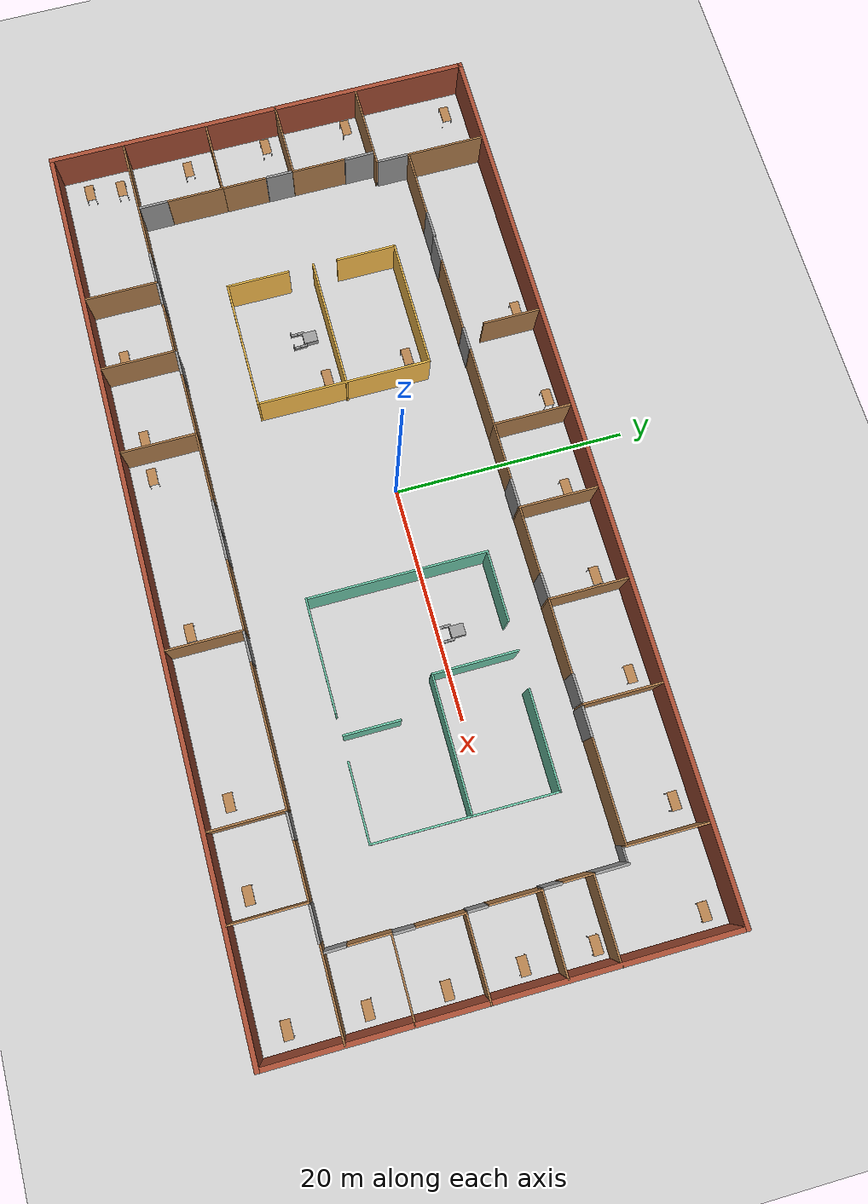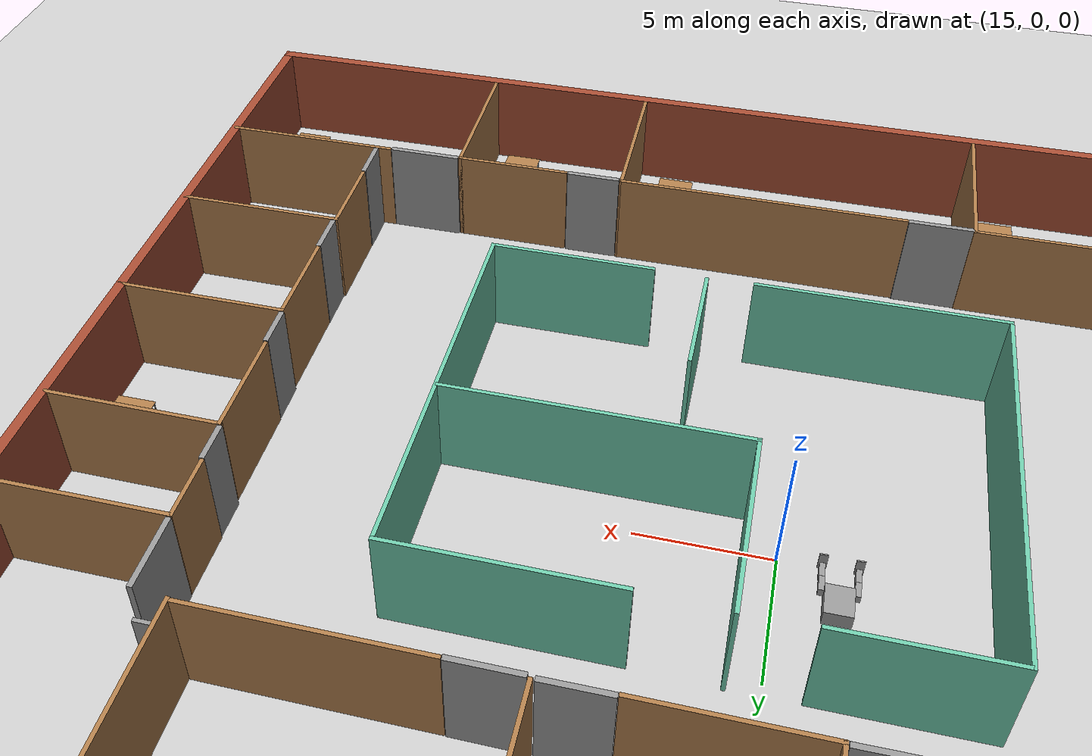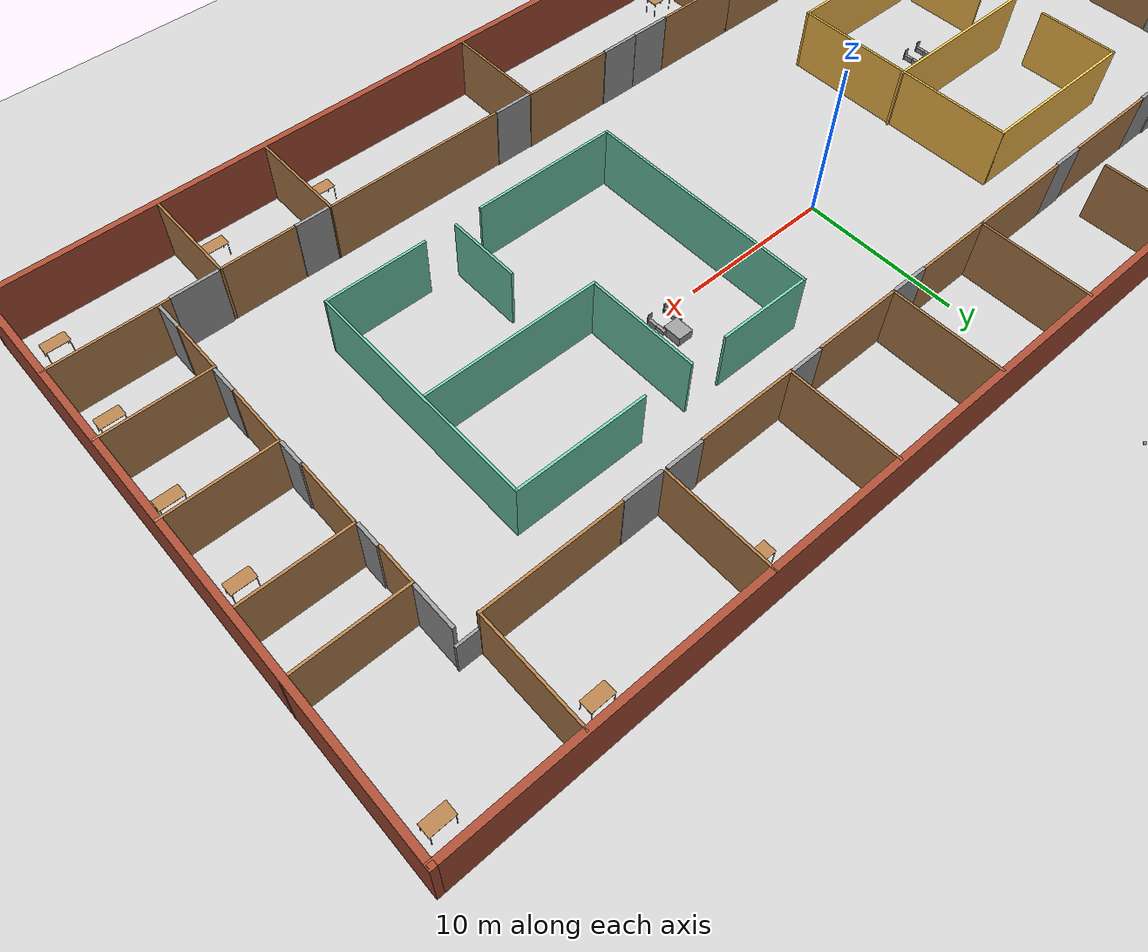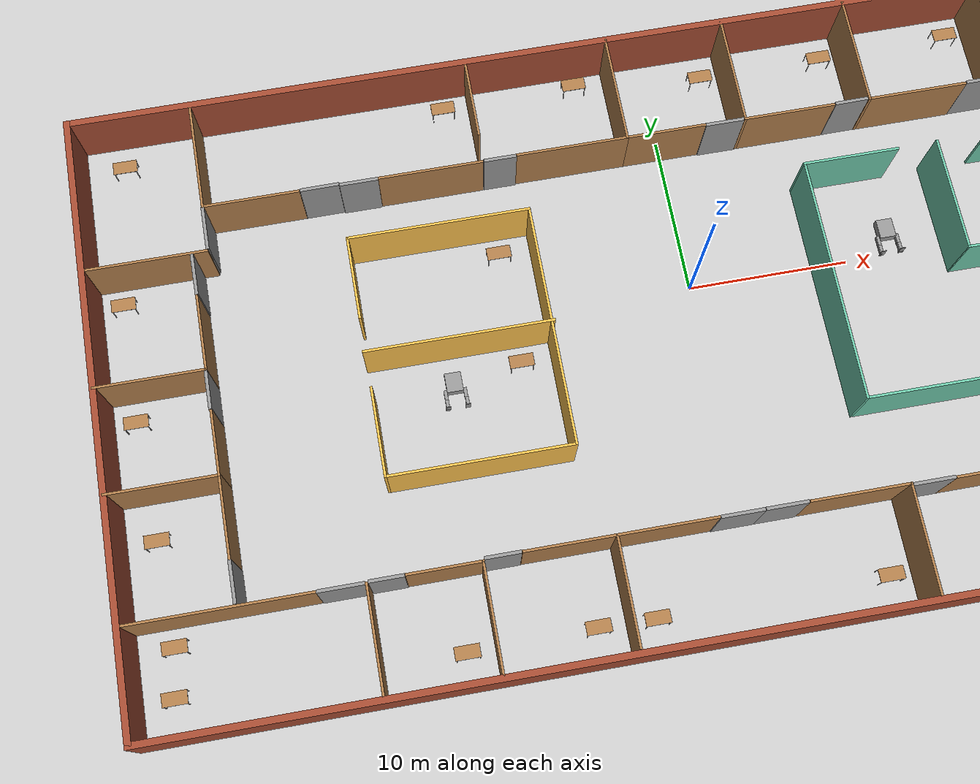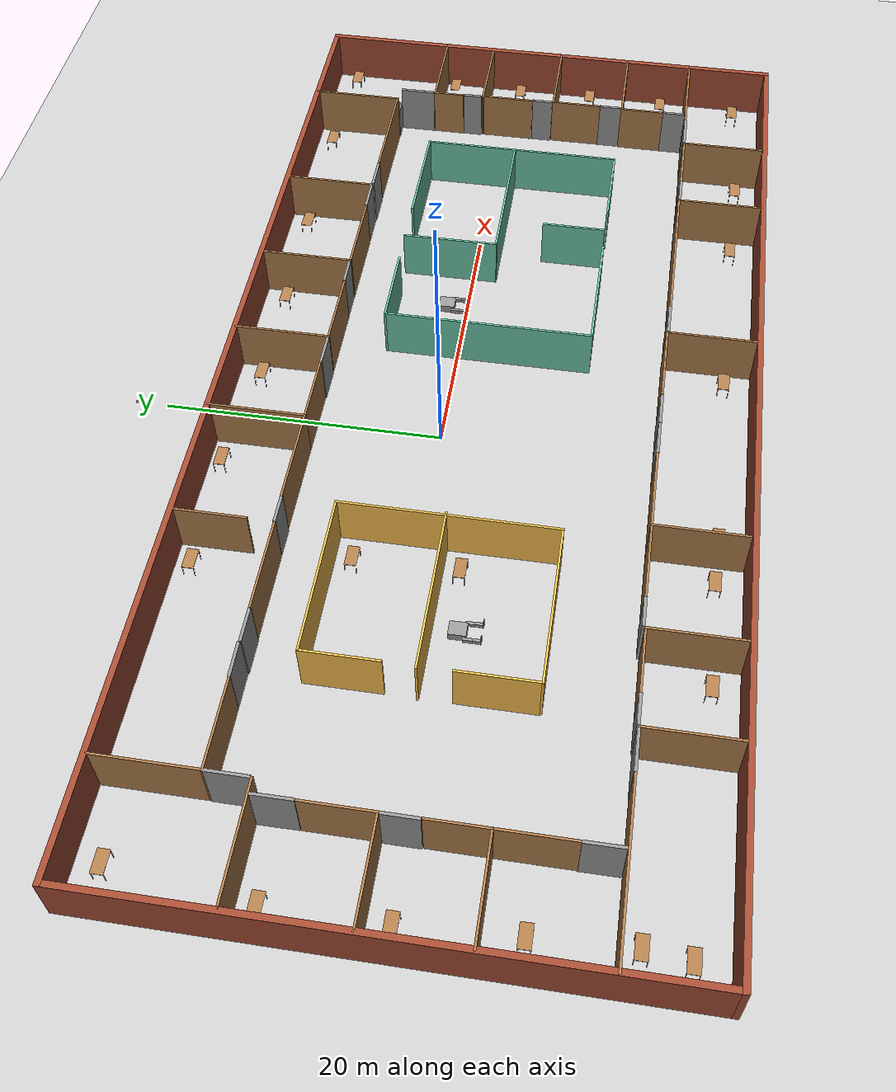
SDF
<sdf version="1.6">
 <world name="default">
  <plugin name="welcome" filename="libwelcome.so"/>
  <light name="sun" type="directional">
   <pose>0 0 10 0 -0 0</pose>
   <diffuse>0.8 0.8 0.8 1</diffuse>
   <specular>0.2 0.2 0.2 1</specular>
   <attenuation>
    <range>1000</range>
    <constant>0.9</constant>
    <linear>0.01</linear>
    <quadratic>0.001</quadratic>
   </attenuation>
   <direction>-0.5 0.1 -0.9</direction>
  </light>
  <model name="ground_plane">
   <static>1</static>
   <link name="link">
    <collision name="collision">
     <geometry><plane><normal>0 0 1</normal><size>100 100</size></plane></geometry>
     <surface><friction><ode><mu>100</mu><mu2>50</mu2></ode></friction></surface>
    </collision>
    <visual name="visual">
     <cast_shadows>0</cast_shadows>
     <geometry><plane><normal>0 0 1</normal><size>100 100</size></plane></geometry>
     <material>
      <script><uri>file://media/materials/scripts/gazebo.material</uri><name>Gazebo/Grey</name></script>
     </material>
    </visual>
   </link>
  </model>
  <gravity>0 0 -9.8</gravity>
  <magnetic_field>6e-06 2.3e-05 -4.2e-05</magnetic_field>
  <atmosphere type="adiabatic"/>
  <physics name="default_physics" default="0" type="ode">
   <max_step_size>0.001</max_step_size>
   <real_time_factor>1</real_time_factor>
   <real_time_update_rate>1000</real_time_update_rate>
  </physics>
  <scene><ambient>0.4 0.4 0.4 1</ambient><background>0.7 0.7 0.7 1</background><shadows>1</shadows></scene>
  <spherical_coordinates>
   <surface_model>EARTH_WGS84</surface_model>
   <latitude_deg>0</latitude_deg>
   <longitude_deg>0</longitude_deg>
   <elevation>0</elevation>
   <heading_deg>0</heading_deg>
  </spherical_coordinates>
  <model name="Building">
   <pose>2.1303 -2.9516 0 0 -0 0</pose>
   <link name="Door_0">
    <collision name="Door_0_Collision">
     <geometry><box><size>2.774 0.2 4</size></box></geometry>
     <pose>0 0 2 0 -0 0</pose>
    </collision>
    <visual name="Door_0_Visual">
     <pose>0 0 2 0 -0 0</pose>
     <geometry><box><size>2.774 0.2 4</size></box></geometry>
     <material>
      <script><uri>file://media/materials/scripts/gazebo.material</uri><name>Gazebo/Grey</name></script>
     </material>
    </visual>
    <pose>-30.849 10.4356 0 0 0 -1.57175</pose>
   </link>
   <link name="Door_1">
    <collision name="Door_1_Collision">
     <geometry><box><size>2.64 0.2 4</size></box></geometry>
     <pose>0 0 2 0 -0 0</pose>
    </collision>
    <visual name="Door_1_Visual">
     <pose>0 0 2 0 -0 0</pose>
     <geometry><box><size>2.64 0.2 4</size></box></geometry>
     <material>
      <script><uri>file://media/materials/scripts/gazebo.material</uri><name>Gazebo/Grey</name></script>
     </material>
    </visual>
    <pose>-31.8238 7.60149 0 0 0 -1.56515</pose>
   </link>
   <link name="Door_10">
    <collision name="Door_10_Collision">
     <geometry><box><size>2.534 0.2 4</size></box></geometry>
     <pose>0 0 2 0 -0 0</pose>
    </collision>
    <visual name="Door_10_Visual">
     <pose>0 0 2 0 -0 0</pose>
     <geometry><box><size>2.534 0.2 4</size></box></geometry>
     <material>
      <script><uri>file://media/materials/scripts/gazebo.material</uri><name>Gazebo/Grey</name></script>
     </material>
    </visual>
    <pose>8.16774 -12.2183 0 0 -0 0</pose>
   </link>
   <link name="Door_11">
    <collision name="Door_11_Collision">
     <geometry><box><size>2.195 0.2 4</size></box></geometry>
     <pose>0 0 2 0 -0 0</pose>
    </collision>
    <visual name="Door_11_Visual">
     <pose>0 0 2 0 -0 0</pose>
     <geometry><box><size>2.195 0.2 4</size></box></geometry>
     <material>
      <script><uri>file://media/materials/scripts/gazebo.material</uri><name>Gazebo/Grey</name></script>
     </material>
    </visual>
    <pose>22.36 -12.2885 0 0 -0 0</pose>
   </link>
   <link name="Door_12">
    <collision name="Door_12_Collision">
     <geometry><box><size>2.963 0.2 4</size></box></geometry>
     <pose>0 0 2 0 -0 0</pose>
    </collision>
    <visual name="Door_12_Visual">
     <pose>0 0 2 0 -0 0</pose>
     <geometry><box><size>2.963 0.2 4</size></box></geometry>
     <material>
      <script><uri>file://media/materials/scripts/gazebo.material</uri><name>Gazebo/Grey</name></script>
     </material>
    </visual>
    <pose>29.7338 -12.2643 0 0 -0 0</pose>
   </link>
   <link name="Door_13">
    <collision name="Door_13_Collision">
     <geometry><box><size>1.77 0.2 4</size></box></geometry>
     <pose>0 0 2 0 -0 0</pose>
    </collision>
    <visual name="Door_13_Visual">
     <pose>0 0 2 0 -0 0</pose>
     <geometry><box><size>1.77 0.2 4</size></box></geometry>
     <material>
      <script><uri>file://media/materials/scripts/gazebo.material</uri><name>Gazebo/Grey</name></script>
     </material>
    </visual>
    <pose>31.8662 -11.2352 0 0 -0 1.57708</pose>
   </link>
   <link name="Door_14">
    <collision name="Door_14_Collision">
     <geometry><box><size>1.73 0.2 4</size></box></geometry>
     <pose>0 0 2 0 -0 0</pose>
    </collision>
    <visual name="Door_14_Visual">
     <pose>0 0 2 0 -0 0</pose>
     <geometry><box><size>1.73 0.2 4</size></box></geometry>
     <material>
      <script><uri>file://media/materials/scripts/gazebo.material</uri><name>Gazebo/Grey</name></script>
     </material>
    </visual>
    <pose>31.9377 -5.93733 0 0 -0 1.5708</pose>
   </link>
   <link name="Door_15">
    <collision name="Door_15_Collision">
     <geometry><box><size>1.629 0.2 4</size></box></geometry>
     <pose>0 0 2 0 -0 0</pose>
    </collision>
    <visual name="Door_15_Visual">
     <pose>0 0 2 0 -0 0</pose>
     <geometry><box><size>1.629 0.2 4</size></box></geometry>
     <material>
      <script><uri>file://media/materials/scripts/gazebo.material</uri><name>Gazebo/Grey</name></script>
     </material>
    </visual>
    <pose>31.8756 -0.212635 0 0 -0 1.57428</pose>
   </link>
   <link name="Door_16">
    <collision name="Door_16_Collision">
     <geometry><box><size>1.525 0.2 4</size></box></geometry>
     <pose>0 0 2 0 -0 0</pose>
    </collision>
    <visual name="Door_16_Visual">
     <pose>0 0 2 0 -0 0</pose>
     <geometry><box><size>1.525 0.2 4</size></box></geometry>
     <material>
      <script><uri>file://media/materials/scripts/gazebo.material</uri><name>Gazebo/Grey</name></script>
     </material>
    </visual>
    <pose>31.7604 5.70164 0 0 -0 1.5708</pose>
   </link>
   <link name="Door_17">
    <collision name="Door_17_Collision">
     <geometry><box><size>2.76245 0.2 4</size></box></geometry>
     <pose>0 0 2 0 -0 0</pose>
    </collision>
    <visual name="Door_17_Visual">
     <pose>0 0 2 0 -0 0</pose>
     <geometry><box><size>2.76245 0.2 4</size></box></geometry>
     <material>
      <script><uri>file://media/materials/scripts/gazebo.material</uri><name>Gazebo/Grey</name></script>
     </material>
    </visual>
    <pose>31.7173 10.407 0 0 -0 1.57411</pose>
   </link>
   <link name="Door_18">
    <collision name="Door_18_Collision">
     <geometry><box><size>2.496 0.2 4</size></box></geometry>
     <pose>0 0 2 0 -0 0</pose>
    </collision>
    <visual name="Door_18_Visual">
     <pose>0 0 2 0 -0 0</pose>
     <geometry><box><size>2.496 0.2 4</size></box></geometry>
     <material>
      <script><uri>file://media/materials/scripts/gazebo.material</uri><name>Gazebo/Grey</name></script>
     </material>
    </visual>
    <pose>20.743 11.9143 0 0 0 -3.14024</pose>
   </link>
   <link name="Door_19">
    <collision name="Door_19_Collision">
     <geometry><box><size>2.35525 0.2 4</size></box></geometry>
     <pose>0 0 2 0 -0 0</pose>
    </collision>
    <visual name="Door_19_Visual">
     <pose>0 0 2 0 -0 0</pose>
     <geometry><box><size>2.35525 0.2 4</size></box></geometry>
     <material>
      <script><uri>file://media/materials/scripts/gazebo.material</uri><name>Gazebo/Grey</name></script>
     </material>
    </visual>
    <pose>18.0916 11.9605 0 0 0 -3.13542</pose>
   </link>
   <link name="Door_2">
    <collision name="Door_2_Collision">
     <geometry><box><size>2.36 0.2 4</size></box></geometry>
     <pose>0 0 2 0 -0 0</pose>
    </collision>
    <visual name="Door_2_Visual">
     <pose>0 0 2 0 -0 0</pose>
     <geometry><box><size>2.36 0.2 4</size></box></geometry>
     <material>
      <script><uri>file://media/materials/scripts/gazebo.material</uri><name>Gazebo/Grey</name></script>
     </material>
    </visual>
    <pose>-31.857 0.312971 0 0 0 -1.57415</pose>
   </link>
   <link name="Door_20">
    <collision name="Door_20_Collision">
     <geometry><box><size>2.08226 0.2 4</size></box></geometry>
     <pose>0 0 2 0 -0 0</pose>
    </collision>
    <visual name="Door_20_Visual">
     <pose>0 0 2 0 -0 0</pose>
     <geometry><box><size>2.08226 0.2 4</size></box></geometry>
     <material>
      <script><uri>file://media/materials/scripts/gazebo.material</uri><name>Gazebo/Grey</name></script>
     </material>
    </visual>
    <pose>9.57215 11.9434 0 0 0 -3.13246</pose>
   </link>
   <link name="Door_21">
    <collision name="Door_21_Collision">
     <geometry><box><size>2.4004 0.2 4</size></box></geometry>
     <pose>0 0 2 0 -0 0</pose>
    </collision>
    <visual name="Door_21_Visual">
     <pose>0 0 2 0 -0 0</pose>
     <geometry><box><size>2.4004 0.2 4</size></box></geometry>
     <material>
      <script><uri>file://media/materials/scripts/gazebo.material</uri><name>Gazebo/Grey</name></script>
     </material>
    </visual>
    <pose>1.52201 11.8997 0 0 -0 3.13892</pose>
   </link>
   <link name="Door_22">
    <collision name="Door_22_Collision">
     <geometry><box><size>2.02176 0.2 4</size></box></geometry>
     <pose>0 0 2 0 -0 0</pose>
    </collision>
    <visual name="Door_22_Visual">
     <pose>0 0 2 0 -0 0</pose>
     <geometry><box><size>2.02176 0.2 4</size></box></geometry>
     <material>
      <script><uri>file://media/materials/scripts/gazebo.material</uri><name>Gazebo/Grey</name></script>
     </material>
    </visual>
    <pose>-12.5547 11.8906 0 0 -0 0</pose>
   </link>
   <link name="Door_23">
    <collision name="Door_23_Collision">
     <geometry><box><size>2.385 0.2 4</size></box></geometry>
     <pose>0 0 2 0 -0 0</pose>
    </collision>
    <visual name="Door_23_Visual">
     <pose>0 0 2 0 -0 0</pose>
     <geometry><box><size>2.385 0.2 4</size></box></geometry>
     <material>
      <script><uri>file://media/materials/scripts/gazebo.material</uri><name>Gazebo/Grey</name></script>
     </material>
    </visual>
    <pose>-21.3031 11.8399 0 0 -0 0</pose>
   </link>
   <link name="Door_24">
    <collision name="Door_24_Collision">
     <geometry><box><size>2.38 0.2 4</size></box></geometry>
     <pose>0 0 2 0 -0 0</pose>
    </collision>
    <visual name="Door_24_Visual">
     <pose>0 0 2 0 -0 0</pose>
     <geometry><box><size>2.38 0.2 4</size></box></geometry>
     <material>
      <script><uri>file://media/materials/scripts/gazebo.material</uri><name>Gazebo/Grey</name></script>
     </material>
    </visual>
    <pose>-23.7055 11.8942 0 0 0 -3.13305</pose>
   </link>
   <link name="Door_3">
    <collision name="Door_3_Collision">
     <geometry><box><size>2.503 0.2 4</size></box></geometry>
     <pose>0 0 2 0 -0 0</pose>
    </collision>
    <visual name="Door_3_Visual">
     <pose>0 0 2 0 -0 0</pose>
     <geometry><box><size>2.503 0.2 4</size></box></geometry>
     <material>
      <script><uri>file://media/materials/scripts/gazebo.material</uri><name>Gazebo/Grey</name></script>
     </material>
    </visual>
    <pose>-31.8314 -11.0051 0 0 0 -1.56499</pose>
   </link>
   <link name="Door_4">
    <collision name="Door_4_Collision">
     <geometry><box><size>2.76 0.2 4</size></box></geometry>
     <pose>0 0 2 0 -0 0</pose>
    </collision>
    <visual name="Door_4_Visual">
     <pose>0 0 2 0 -0 0</pose>
     <geometry><box><size>2.76 0.2 4</size></box></geometry>
     <material>
      <script><uri>file://media/materials/scripts/gazebo.material</uri><name>Gazebo/Grey</name></script>
     </material>
    </visual>
    <pose>-25.9426 -12.3476 0 0 -0 0</pose>
   </link>
   <link name="Door_6">
    <collision name="Door_6_Collision">
     <geometry><box><size>2.064 0.2 4</size></box></geometry>
     <pose>0 0 2 0 -0 0</pose>
    </collision>
    <visual name="Door_6_Visual">
     <pose>0 0 2 0 -0 0</pose>
     <geometry><box><size>2.064 0.2 4</size></box></geometry>
     <material>
      <script><uri>file://media/materials/scripts/gazebo.material</uri><name>Gazebo/Grey</name></script>
     </material>
    </visual>
    <pose>-23.3644 -12.2986 0 0 -0 0</pose>
   </link>
   <link name="Door_7">
    <collision name="Door_7_Collision">
     <geometry><box><size>2.14008 0.2 4</size></box></geometry>
     <pose>0 0 2 0 -0 0</pose>
    </collision>
    <visual name="Door_7_Visual">
     <pose>0 0 2 0 -0 0</pose>
     <geometry><box><size>2.14008 0.2 4</size></box></geometry>
     <material>
      <script><uri>file://media/materials/scripts/gazebo.material</uri><name>Gazebo/Grey</name></script>
     </material>
    </visual>
    <pose>-16.7382 -12.1348 0 0 -0 0</pose>
   </link>
   <link name="Door_8">
    <collision name="Door_8_Collision">
     <geometry><box><size>2.518 0.2 4</size></box></geometry>
     <pose>0 0 2 0 -0 0</pose>
    </collision>
    <visual name="Door_8_Visual">
     <pose>0 0 2 0 -0 0</pose>
     <geometry><box><size>2.518 0.2 4</size></box></geometry>
     <material>
      <script><uri>file://media/materials/scripts/gazebo.material</uri><name>Gazebo/Grey</name></script>
     </material>
    </visual>
    <pose>-0.38717 -12.1484 0 0 -0 0</pose>
   </link>
   <link name="Door_9">
    <collision name="Door_9_Collision">
     <geometry><box><size>2.596 0.2 4</size></box></geometry>
     <pose>0 0 2 0 -0 0</pose>
    </collision>
    <visual name="Door_9_Visual">
     <pose>0 0 2 0 -0 0</pose>
     <geometry><box><size>2.596 0.2 4</size></box></geometry>
     <material>
      <script><uri>file://media/materials/scripts/gazebo.material</uri><name>Gazebo/Grey</name></script>
     </material>
    </visual>
    <pose>-2.96764 -12.1539 0 0 0 -3.14159</pose>
   </link>
   <link name="Wall_212">
    <collision name="Wall_212_Collision">
     <geometry><box><size>77.2499 0.4 4</size></box></geometry>
     <pose>0 0 2 0 -0 0</pose>
    </collision>
    <visual name="Wall_212_Visual">
     <pose>0 0 2 0 -0 0</pose>
     <geometry><box><size>77.2499 0.4 4</size></box></geometry>
     <material>
      <script><uri>file://media/materials/scripts/gazebo.material</uri><name>Gazebo/Bricks</name></script>
      <ambient>1 1 1 1</ambient>
     </material>
     <meta><layer>0</layer></meta>
    </visual>
    <pose>-0.008498 18.8 0 0 -0 0</pose>
   </link>
   <link name="Wall_213">
    <collision name="Wall_213_Collision">
     <geometry><box><size>38.0003 0.4 4</size></box></geometry>
     <pose>0 0 2 0 -0 0</pose>
    </collision>
    <visual name="Wall_213_Visual">
     <pose>0 0 2 0 -0 0</pose>
     <geometry><box><size>38.0003 0.4 4</size></box></geometry>
     <material>
      <script><uri>file://media/materials/scripts/gazebo.material</uri><name>Gazebo/Bricks</name></script>
      <ambient>1 1 1 1</ambient>
     </material>
     <meta><layer>0</layer></meta>
    </visual>
    <pose>38.4165 -1e-06 0 0 0 -1.5708</pose>
   </link>
   <link name="Wall_214">
    <collision name="Wall_214_Collision">
     <geometry><box><size>77.25 0.4 4</size></box></geometry>
     <pose>0 0 2 0 -0 0</pose>
    </collision>
    <visual name="Wall_214_Visual">
     <pose>0 0 2 0 -0 0</pose>
     <geometry><box><size>77.25 0.4 4</size></box></geometry>
     <material>
      <script><uri>file://media/materials/scripts/gazebo.material</uri><name>Gazebo/Bricks</name></script>
      <ambient>1 1 1 1</ambient>
     </material>
     <meta><layer>0</layer></meta>
    </visual>
    <pose>-0.008498 -18.8 0 0 -0 3.14159</pose>
   </link>
   <link name="Wall_215">
    <collision name="Wall_215_Collision">
     <geometry><box><size>37.9997 0.4 4</size></box></geometry>
     <pose>0 0 2 0 -0 0</pose>
    </collision>
    <visual name="Wall_215_Visual">
     <pose>0 0 2 0 -0 0</pose>
     <geometry><box><size>37.9997 0.4 4</size></box></geometry>
     <material>
      <script><uri>file://media/materials/scripts/gazebo.material</uri><name>Gazebo/Bricks</name></script>
      <ambient>1 1 1 1</ambient>
     </material>
     <meta><layer>0</layer></meta>
    </visual>
    <pose>-38.4335 -1e-06 0 0 -0 1.5708</pose>
   </link>
   <link name="Wall_218">
    <collision name="Wall_218_Collision">
     <geometry><box><size>7.75 0.15 4</size></box></geometry>
     <pose>0 0 2 0 -0 0</pose>
    </collision>
    <visual name="Wall_218_Visual">
     <pose>0 0 2 0 -0 0</pose>
     <geometry><box><size>7.75 0.15 4</size></box></geometry>
     <material>
      <script><uri>file://media/materials/scripts/gazebo.material</uri><name>Gazebo/Wood</name></script>
      <ambient>1 1 1 1</ambient>
     </material>
     <meta><layer>0</layer></meta>
    </visual>
    <pose>-34.7005 8.965 0 0 -0 0</pose>
   </link>
   <link name="Wall_220">
    <collision name="Wall_220_Collision">
     <geometry><box><size>6.75 0.15 4</size></box></geometry>
     <pose>0 0 2 0 -0 0</pose>
    </collision>
    <visual name="Wall_220_Visual">
     <pose>0 0 2 0 -0 0</pose>
     <geometry><box><size>6.75 0.15 4</size></box></geometry>
     <material>
      <script><uri>file://media/materials/scripts/gazebo.material</uri><name>Gazebo/Wood</name></script>
      <ambient>1 1 1 1</ambient>
     </material>
     <meta><layer>0</layer></meta>
    </visual>
    <pose>-35.1305 1.578 0 0 -0 0</pose>
   </link>
   <link name="Wall_221">
    <collision name="Wall_221_Collision">
     <geometry><box><size>4.75 0.15 4</size></box></geometry>
     <pose>0 0 2 0 -0 0</pose>
    </collision>
    <visual name="Wall_221_Visual">
     <pose>0 0 2 0 -0 0</pose>
     <geometry><box><size>4.75 0.15 4</size></box></geometry>
     <material>
      <script><uri>file://media/materials/scripts/gazebo.material</uri><name>Gazebo/Wood</name></script>
      <ambient>1 1 1 1</ambient>
     </material>
     <meta><layer>0</layer></meta>
    </visual>
    <pose>-31.8305 3.878 0 0 -0 1.5708</pose>
   </link>
   <link name="Wall_223">
    <collision name="Wall_223_Collision">
     <geometry><box><size>6.75 0.15 4</size></box></geometry>
     <pose>0 0 2 0 -0 0</pose>
    </collision>
    <visual name="Wall_223_Visual">
     <pose>0 0 2 0 -0 0</pose>
     <geometry><box><size>6.75 0.15 4</size></box></geometry>
     <material>
      <script><uri>file://media/materials/scripts/gazebo.material</uri><name>Gazebo/Wood</name></script>
      <ambient>1 1 1 1</ambient>
     </material>
     <meta><layer>0</layer></meta>
    </visual>
    <pose>-35.1305 -4.825 0 0 -0 0</pose>
   </link>
   <link name="Wall_224">
    <collision name="Wall_224_Collision">
     <geometry><box><size>4 0.15 4</size></box></geometry>
     <pose>0 0 2 0 -0 0</pose>
    </collision>
    <visual name="Wall_224_Visual">
     <pose>0 0 2 0 -0 0</pose>
     <geometry><box><size>4 0.15 4</size></box></geometry>
     <material>
      <script><uri>file://media/materials/scripts/gazebo.material</uri><name>Gazebo/Wood</name></script>
      <ambient>1 1 1 1</ambient>
     </material>
     <meta><layer>0</layer></meta>
    </visual>
    <pose>-31.8305 -2.9 0 0 -0 1.5708</pose>
   </link>
   <link name="Wall_226">
    <collision name="Wall_226_Collision">
     <geometry><box><size>5 0.15 4</size></box></geometry>
     <pose>0 0 2 0 -0 0</pose>
    </collision>
    <visual name="Wall_226_Visual">
     <pose>0 0 2 0 -0 0</pose>
     <geometry><box><size>5 0.15 4</size></box></geometry>
     <material>
      <script><uri>file://media/materials/scripts/gazebo.material</uri><name>Gazebo/Wood</name></script>
      <ambient>1 1 1 1</ambient>
     </material>
     <meta><layer>0</layer></meta>
    </visual>
    <pose>-31.8305 -7.25 0 0 0 -1.5708</pose>
   </link>
   <link name="Wall_228">
    <collision name="Wall_228_Collision">
     <geometry><box><size>11.25 0.15 4</size></box></geometry>
     <pose>0 0 2 0 -0 0</pose>
    </collision>
    <visual name="Wall_228_Visual">
     <pose>0 0 2 0 -0 0</pose>
     <geometry><box><size>11.25 0.15 4</size></box></geometry>
     <material>
      <script><uri>file://media/materials/scripts/gazebo.material</uri><name>Gazebo/Wood</name></script>
      <ambient>1 1 1 1</ambient>
     </material>
     <meta><layer>0</layer></meta>
    </visual>
    <pose>-32.9505 -12.353 0 0 -0 0</pose>
   </link>
   <link name="Wall_230">
    <collision name="Wall_230_Collision">
     <geometry><box><size>6.35 0.15 4</size></box></geometry>
     <pose>0 0 2 0 -0 0</pose>
    </collision>
    <visual name="Wall_230_Visual">
     <pose>0 0 2 0 -0 0</pose>
     <geometry><box><size>6.35 0.15 4</size></box></geometry>
     <material>
      <script><uri>file://media/materials/scripts/gazebo.material</uri><name>Gazebo/Wood</name></script>
      <ambient>1 1 1 1</ambient>
     </material>
     <meta><layer>0</layer></meta>
    </visual>
    <pose>-24.4995 -15.462 0 0 0 -1.5708</pose>
   </link>
   <link name="Wall_232">
    <collision name="Wall_232_Collision">
     <geometry><box><size>6.5 0.15 4</size></box></geometry>
     <pose>0 0 2 0 -0 0</pose>
    </collision>
    <visual name="Wall_232_Visual">
     <pose>0 0 2 0 -0 0</pose>
     <geometry><box><size>6.5 0.15 4</size></box></geometry>
     <material>
      <script><uri>file://media/materials/scripts/gazebo.material</uri><name>Gazebo/Wood</name></script>
      <ambient>1 1 1 1</ambient>
     </material>
     <meta><layer>0</layer></meta>
    </visual>
    <pose>-17.8855 -15.458 0 0 0 -1.5708</pose>
   </link>
   <link name="Wall_234">
    <collision name="Wall_234_Collision">
     <geometry><box><size>5.5 0.15 4</size></box></geometry>
     <pose>0 0 2 0 -0 0</pose>
    </collision>
    <visual name="Wall_234_Visual">
     <pose>0 0 2 0 -0 0</pose>
     <geometry><box><size>5.5 0.15 4</size></box></geometry>
     <material>
      <script><uri>file://media/materials/scripts/gazebo.material</uri><name>Gazebo/Wood</name></script>
      <ambient>1 1 1 1</ambient>
     </material>
     <meta><layer>0</layer></meta>
    </visual>
    <pose>-12.8895 -12.142 0 0 -0 0</pose>
   </link>
   <link name="Wall_235">
    <collision name="Wall_235_Collision">
     <geometry><box><size>6.5 0.15 4</size></box></geometry>
     <pose>0 0 2 0 -0 0</pose>
    </collision>
    <visual name="Wall_235_Visual">
     <pose>0 0 2 0 -0 0</pose>
     <geometry><box><size>6.5 0.15 4</size></box></geometry>
     <material>
      <script><uri>file://media/materials/scripts/gazebo.material</uri><name>Gazebo/Wood</name></script>
      <ambient>1 1 1 1</ambient>
     </material>
     <meta><layer>0</layer></meta>
    </visual>
    <pose>-10.2145 -15.317 0 0 0 -1.5708</pose>
   </link>
   <link name="Wall_237">
    <collision name="Wall_237_Collision">
     <geometry><box><size>6 0.15 4</size></box></geometry>
     <pose>0 0 2 0 -0 0</pose>
    </collision>
    <visual name="Wall_237_Visual">
     <pose>0 0 2 0 -0 0</pose>
     <geometry><box><size>6 0.15 4</size></box></geometry>
     <material>
      <script><uri>file://media/materials/scripts/gazebo.material</uri><name>Gazebo/Wood</name></script>
      <ambient>1 1 1 1</ambient>
     </material>
     <meta><layer>0</layer></meta>
    </visual>
    <pose>-7.2895 -12.142 0 0 -0 0</pose>
   </link>
   <link name="Wall_239">
    <collision name="Wall_239_Collision">
     <geometry><box><size>6 0.15 4</size></box></geometry>
     <pose>0 0 2 0 -0 0</pose>
    </collision>
    <visual name="Wall_239_Visual">
     <pose>0 0 2 0 -0 0</pose>
     <geometry><box><size>6 0.15 4</size></box></geometry>
     <material>
      <script><uri>file://media/materials/scripts/gazebo.material</uri><name>Gazebo/Wood</name></script>
      <ambient>1 1 1 1</ambient>
     </material>
     <meta><layer>0</layer></meta>
    </visual>
    <pose>3.90962 -12.1515 0 0 -0 0</pose>
   </link>
   <link name="Wall_240">
    <collision name="Wall_240_Collision">
     <geometry><box><size>6.54539 0.15 4</size></box></geometry>
     <pose>0 0 2 0 -0 0</pose>
    </collision>
    <visual name="Wall_240_Visual">
     <pose>0 0 2 0 -0 0</pose>
     <geometry><box><size>6.54539 0.15 4</size></box></geometry>
     <material>
      <script><uri>file://media/materials/scripts/gazebo.material</uri><name>Gazebo/Wood</name></script>
      <ambient>1 1 1 1</ambient>
     </material>
     <meta><layer>0</layer></meta>
    </visual>
    <pose>6.82706 -15.3643 0 0 0 -1.57316</pose>
   </link>
   <link name="Wall_242">
    <collision name="Wall_242_Collision">
     <geometry><box><size>11.75 0.15 4</size></box></geometry>
     <pose>0 0 2 0 -0 0</pose>
    </collision>
    <visual name="Wall_242_Visual">
     <pose>0 0 2 0 -0 0</pose>
     <geometry><box><size>11.75 0.15 4</size></box></geometry>
     <material>
      <script><uri>file://media/materials/scripts/gazebo.material</uri><name>Gazebo/Wood</name></script>
      <ambient>1 1 1 1</ambient>
     </material>
     <meta><layer>0</layer></meta>
    </visual>
    <pose>15.3208 -12.2422 0 0 -0 0</pose>
   </link>
   <link name="Wall_243">
    <collision name="Wall_243_Collision">
     <geometry><box><size>6.46979 0.15 4</size></box></geometry>
     <pose>0 0 2 0 -0 0</pose>
    </collision>
    <visual name="Wall_243_Visual">
     <pose>0 0 2 0 -0 0</pose>
     <geometry><box><size>6.46979 0.15 4</size></box></geometry>
     <material>
      <script><uri>file://media/materials/scripts/gazebo.material</uri><name>Gazebo/Wood</name></script>
      <ambient>1 1 1 1</ambient>
     </material>
     <meta><layer>0</layer></meta>
    </visual>
    <pose>21.1667 -15.4021 0 0 0 -1.56736</pose>
   </link>
   <link name="Wall_245">
    <collision name="Wall_245_Collision">
     <geometry><box><size>4.75 0.15 4</size></box></geometry>
     <pose>0 0 2 0 -0 0</pose>
    </collision>
    <visual name="Wall_245_Visual">
     <pose>0 0 2 0 -0 0</pose>
     <geometry><box><size>4.75 0.15 4</size></box></geometry>
     <material>
      <script><uri>file://media/materials/scripts/gazebo.material</uri><name>Gazebo/Wood</name></script>
      <ambient>1 1 1 1</ambient>
     </material>
     <meta><layer>0</layer></meta>
    </visual>
    <pose>25.8545 -12.283 0 0 -0 0</pose>
   </link>
   <link name="Wall_246">
    <collision name="Wall_246_Collision">
     <geometry><box><size>6.5 0.15 4</size></box></geometry>
     <pose>0 0 2 0 -0 0</pose>
    </collision>
    <visual name="Wall_246_Visual">
     <pose>0 0 2 0 -0 0</pose>
     <geometry><box><size>6.5 0.15 4</size></box></geometry>
     <material>
      <script><uri>file://media/materials/scripts/gazebo.material</uri><name>Gazebo/Wood</name></script>
      <ambient>1 1 1 1</ambient>
     </material>
     <meta><layer>0</layer></meta>
    </visual>
    <pose>28.1545 -15.458 0 0 0 -1.5708</pose>
   </link>
   <link name="Wall_248">
    <collision name="Wall_248_Collision">
     <geometry><box><size>7.25 0.15 4</size></box></geometry>
     <pose>0 0 2 0 -0 0</pose>
    </collision>
    <visual name="Wall_248_Visual">
     <pose>0 0 2 0 -0 0</pose>
     <geometry><box><size>7.25 0.15 4</size></box></geometry>
     <material>
      <script><uri>file://media/materials/scripts/gazebo.material</uri><name>Gazebo/Wood</name></script>
      <ambient>1 1 1 1</ambient>
     </material>
     <meta><layer>0</layer></meta>
    </visual>
    <pose>34.8487 -12.2236 0 0 -0 0</pose>
   </link>
   <link name="Wall_250">
    <collision name="Wall_250_Collision">
     <geometry><box><size>3.5 0.15 4</size></box></geometry>
     <pose>0 0 2 0 -0 0</pose>
    </collision>
    <visual name="Wall_250_Visual">
     <pose>0 0 2 0 -0 0</pose>
     <geometry><box><size>3.5 0.15 4</size></box></geometry>
     <material>
      <script><uri>file://media/materials/scripts/gazebo.material</uri><name>Gazebo/Wood</name></script>
      <ambient>1 1 1 1</ambient>
     </material>
     <meta><layer>0</layer></meta>
    </visual>
    <pose>31.8485 -8.578 0 0 -0 1.5708</pose>
   </link>
   <link name="Wall_251">
    <collision name="Wall_251_Collision">
     <geometry><box><size>6.75 0.15 4</size></box></geometry>
     <pose>0 0 2 0 -0 0</pose>
    </collision>
    <visual name="Wall_251_Visual">
     <pose>0 0 2 0 -0 0</pose>
     <geometry><box><size>6.75 0.15 4</size></box></geometry>
     <material>
      <script><uri>file://media/materials/scripts/gazebo.material</uri><name>Gazebo/Wood</name></script>
      <ambient>1 1 1 1</ambient>
     </material>
     <meta><layer>0</layer></meta>
    </visual>
    <pose>35.1485 -6.903 0 0 -0 0</pose>
   </link>
   <link name="Wall_253">
    <collision name="Wall_253_Collision">
     <geometry><box><size>4 0.15 4</size></box></geometry>
     <pose>0 0 2 0 -0 0</pose>
    </collision>
    <visual name="Wall_253_Visual">
     <pose>0 0 2 0 -0 0</pose>
     <geometry><box><size>4 0.15 4</size></box></geometry>
     <material>
      <script><uri>file://media/materials/scripts/gazebo.material</uri><name>Gazebo/Wood</name></script>
      <ambient>1 1 1 1</ambient>
     </material>
     <meta><layer>0</layer></meta>
    </visual>
    <pose>31.9195 -3.051 0 0 -0 1.5708</pose>
   </link>
   <link name="Wall_254">
    <collision name="Wall_254_Collision">
     <geometry><box><size>6.75 0.15 4</size></box></geometry>
     <pose>0 0 2 0 -0 0</pose>
    </collision>
    <visual name="Wall_254_Visual">
     <pose>0 0 2 0 -0 0</pose>
     <geometry><box><size>6.75 0.15 4</size></box></geometry>
     <material>
      <script><uri>file://media/materials/scripts/gazebo.material</uri><name>Gazebo/Wood</name></script>
      <ambient>1 1 1 1</ambient>
     </material>
     <meta><layer>0</layer></meta>
    </visual>
    <pose>35.2195 -1.126 0 0 -0 0</pose>
   </link>
   <link name="Wall_256">
    <collision name="Wall_256_Collision">
     <geometry><box><size>4.25 0.15 4</size></box></geometry>
     <pose>0 0 2 0 -0 0</pose>
    </collision>
    <visual name="Wall_256_Visual">
     <pose>0 0 2 0 -0 0</pose>
     <geometry><box><size>4.25 0.15 4</size></box></geometry>
     <material>
      <script><uri>file://media/materials/scripts/gazebo.material</uri><name>Gazebo/Wood</name></script>
      <ambient>1 1 1 1</ambient>
     </material>
     <meta><layer>0</layer></meta>
    </visual>
    <pose>31.8299 2.773 0 0 -0 1.5708</pose>
   </link>
   <link name="Wall_257">
    <collision name="Wall_257_Collision">
     <geometry><box><size>6.62866 0.15 4</size></box></geometry>
     <pose>0 0 2 0 -0 0</pose>
    </collision>
    <visual name="Wall_257_Visual">
     <pose>0 0 2 0 -0 0</pose>
     <geometry><box><size>6.62866 0.15 4</size></box></geometry>
     <material>
      <script><uri>file://media/materials/scripts/gazebo.material</uri><name>Gazebo/Wood</name></script>
      <ambient>1 1 1 1</ambient>
     </material>
     <meta><layer>0</layer></meta>
    </visual>
    <pose>35.0692 4.83311 0 0 0 -0.003122</pose>
   </link>
   <link name="Wall_259">
    <collision name="Wall_259_Collision">
     <geometry><box><size>2.5 0.15 4</size></box></geometry>
     <pose>0 0 2 0 -0 0</pose>
    </collision>
    <visual name="Wall_259_Visual">
     <pose>0 0 2 0 -0 0</pose>
     <geometry><box><size>2.5 0.15 4</size></box></geometry>
     <material>
      <script><uri>file://media/materials/scripts/gazebo.material</uri><name>Gazebo/Wood</name></script>
      <ambient>1 1 1 1</ambient>
     </material>
     <meta><layer>0</layer></meta>
    </visual>
    <pose>31.7085 7.738 0 0 -0 1.5708</pose>
   </link>
   <link name="Wall_260">
    <collision name="Wall_260_Collision">
     <geometry><box><size>7 0.15 4</size></box></geometry>
     <pose>0 0 2 0 -0 0</pose>
    </collision>
    <visual name="Wall_260_Visual">
     <pose>0 0 2 0 -0 0</pose>
     <geometry><box><size>7 0.15 4</size></box></geometry>
     <material>
      <script><uri>file://media/materials/scripts/gazebo.material</uri><name>Gazebo/Wood</name></script>
      <ambient>1 1 1 1</ambient>
     </material>
     <meta><layer>0</layer></meta>
    </visual>
    <pose>35.1335 8.913 0 0 -0 0</pose>
   </link>
   <link name="Wall_263">
    <collision name="Wall_263_Collision">
     <geometry><box><size>7.05939 0.15 4</size></box></geometry>
     <pose>0 0 2 0 -0 0</pose>
    </collision>
    <visual name="Wall_263_Visual">
     <pose>0 0 2 0 -0 0</pose>
     <geometry><box><size>7.05939 0.15 4</size></box></geometry>
     <material>
      <script><uri>file://media/materials/scripts/gazebo.material</uri><name>Gazebo/Wood</name></script>
      <ambient>1 1 1 1</ambient>
     </material>
     <meta><layer>0</layer></meta>
    </visual>
    <pose>30.4415 15.3503 0 0 0 -1.5708</pose>
   </link>
   <link name="Wall_264">
    <collision name="Wall_264_Collision">
     <geometry><box><size>8.5 0.15 4</size></box></geometry>
     <pose>0 0 2 0 -0 0</pose>
    </collision>
    <visual name="Wall_264_Visual">
     <pose>0 0 2 0 -0 0</pose>
     <geometry><box><size>8.5 0.15 4</size></box></geometry>
     <material>
      <script><uri>file://media/materials/scripts/gazebo.material</uri><name>Gazebo/Wood</name></script>
      <ambient>1 1 1 1</ambient>
     </material>
     <meta><layer>0</layer></meta>
    </visual>
    <pose>26.2665 11.9266 0 0 -0 3.14159</pose>
   </link>
   <link name="Wall_266">
    <collision name="Wall_266_Collision">
     <geometry><box><size>7 0.15 4</size></box></geometry>
     <pose>0 0 2 0 -0 0</pose>
    </collision>
    <visual name="Wall_266_Visual">
     <pose>0 0 2 0 -0 0</pose>
     <geometry><box><size>7 0.15 4</size></box></geometry>
     <material>
      <script><uri>file://media/materials/scripts/gazebo.material</uri><name>Gazebo/Wood</name></script>
      <ambient>1 1 1 1</ambient>
     </material>
     <meta><layer>0</layer></meta>
    </visual>
    <pose>19.3955 15.45 0 0 0 -1.5708</pose>
   </link>
   <link name="Wall_268">
    <collision name="Wall_268_Collision">
     <geometry><box><size>6.25 0.15 4</size></box></geometry>
     <pose>0 0 2 0 -0 0</pose>
    </collision>
    <visual name="Wall_268_Visual">
     <pose>0 0 2 0 -0 0</pose>
     <geometry><box><size>6.25 0.15 4</size></box></geometry>
     <material>
      <script><uri>file://media/materials/scripts/gazebo.material</uri><name>Gazebo/Wood</name></script>
      <ambient>1 1 1 1</ambient>
     </material>
     <meta><layer>0</layer></meta>
    </visual>
    <pose>13.7665 11.91 0 0 -0 3.14159</pose>
   </link>
   <link name="Wall_269">
    <collision name="Wall_269_Collision">
     <geometry><box><size>7 0.15 4</size></box></geometry>
     <pose>0 0 2 0 -0 0</pose>
    </collision>
    <visual name="Wall_269_Visual">
     <pose>0 0 2 0 -0 0</pose>
     <geometry><box><size>7 0.15 4</size></box></geometry>
     <material>
      <script><uri>file://media/materials/scripts/gazebo.material</uri><name>Gazebo/Wood</name></script>
      <ambient>1 1 1 1</ambient>
     </material>
     <meta><layer>0</layer></meta>
    </visual>
    <pose>10.7165 15.335 0 0 -0 1.5708</pose>
   </link>
   <link name="Wall_271">
    <collision name="Wall_271_Collision">
     <geometry><box><size>5.75 0.15 4</size></box></geometry>
     <pose>0 0 2 0 -0 0</pose>
    </collision>
    <visual name="Wall_271_Visual">
     <pose>0 0 2 0 -0 0</pose>
     <geometry><box><size>5.75 0.15 4</size></box></geometry>
     <material>
      <script><uri>file://media/materials/scripts/gazebo.material</uri><name>Gazebo/Wood</name></script>
      <ambient>1 1 1 1</ambient>
     </material>
     <meta><layer>0</layer></meta>
    </visual>
    <pose>5.6175 11.895 0 0 -0 3.14159</pose>
   </link>
   <link name="Wall_272">
    <collision name="Wall_272_Collision">
     <geometry><box><size>7 0.15 4</size></box></geometry>
     <pose>0 0 2 0 -0 0</pose>
    </collision>
    <visual name="Wall_272_Visual">
     <pose>0 0 2 0 -0 0</pose>
     <geometry><box><size>7 0.15 4</size></box></geometry>
     <material>
      <script><uri>file://media/materials/scripts/gazebo.material</uri><name>Gazebo/Wood</name></script>
      <ambient>1 1 1 1</ambient>
     </material>
     <meta><layer>0</layer></meta>
    </visual>
    <pose>2.8175 15.32 0 0 -0 1.5708</pose>
   </link>
   <link name="Wall_274">
    <collision name="Wall_274_Collision">
     <geometry><box><size>5 0.15 4</size></box></geometry>
     <pose>0 0 2 0 -0 0</pose>
    </collision>
    <visual name="Wall_274_Visual">
     <pose>0 0 2 0 -0 0</pose>
     <geometry><box><size>5 0.15 4</size></box></geometry>
     <material>
      <script><uri>file://media/materials/scripts/gazebo.material</uri><name>Gazebo/Wood</name></script>
      <ambient>1 1 1 1</ambient>
     </material>
     <meta><layer>0</layer></meta>
    </visual>
    <pose>-2.1885 11.925 0 0 -0 3.14159</pose>
   </link>
   <link name="Wall_275">
    <collision name="Wall_275_Collision">
     <geometry><box><size>7 0.15 4</size></box></geometry>
     <pose>0 0 2 0 -0 0</pose>
    </collision>
    <visual name="Wall_275_Visual">
     <pose>0 0 2 0 -0 0</pose>
     <geometry><box><size>7 0.15 4</size></box></geometry>
     <material>
      <script><uri>file://media/materials/scripts/gazebo.material</uri><name>Gazebo/Wood</name></script>
      <ambient>1 1 1 1</ambient>
     </material>
     <meta><layer>0</layer></meta>
    </visual>
    <pose>-4.6135 15.35 0 0 -0 1.5708</pose>
   </link>
   <link name="Wall_277">
    <collision name="Wall_277_Collision">
     <geometry><box><size>7 0.15 4</size></box></geometry>
     <pose>0 0 2 0 -0 0</pose>
    </collision>
    <visual name="Wall_277_Visual">
     <pose>0 0 2 0 -0 0</pose>
     <geometry><box><size>7 0.15 4</size></box></geometry>
     <material>
      <script><uri>file://media/materials/scripts/gazebo.material</uri><name>Gazebo/Wood</name></script>
      <ambient>1 1 1 1</ambient>
     </material>
     <meta><layer>0</layer></meta>
    </visual>
    <pose>-8.0385 11.925 0 0 -0 3.14159</pose>
   </link>
   <link name="Wall_279">
    <collision name="Wall_279_Collision">
     <geometry><box><size>5.25 0.15 4</size></box></geometry>
     <pose>0 0 2 0 -0 0</pose>
    </collision>
    <visual name="Wall_279_Visual">
     <pose>0 0 2 0 -0 0</pose>
     <geometry><box><size>5.25 0.15 4</size></box></geometry>
     <material>
      <script><uri>file://media/materials/scripts/gazebo.material</uri><name>Gazebo/Wood</name></script>
      <ambient>1 1 1 1</ambient>
     </material>
     <meta><layer>0</layer></meta>
    </visual>
    <pose>-13.5545 16.302 0 0 -0 1.5708</pose>
   </link>
   <link name="Wall_281">
    <collision name="Wall_281_Collision">
     <geometry><box><size>6.5 0.15 4</size></box></geometry>
     <pose>0 0 2 0 -0 0</pose>
    </collision>
    <visual name="Wall_281_Visual">
     <pose>0 0 2 0 -0 0</pose>
     <geometry><box><size>6.5 0.15 4</size></box></geometry>
     <material>
      <script><uri>file://media/materials/scripts/gazebo.material</uri><name>Gazebo/Wood</name></script>
      <ambient>1 1 1 1</ambient>
     </material>
     <meta><layer>0</layer></meta>
    </visual>
    <pose>-16.8595 11.861 0 0 -0 3.14159</pose>
   </link>
   <link name="Wall_283">
    <collision name="Wall_283_Collision">
     <geometry><box><size>6 0.15 4</size></box></geometry>
     <pose>0 0 2 0 -0 0</pose>
    </collision>
    <visual name="Wall_283_Visual">
     <pose>0 0 2 0 -0 0</pose>
     <geometry><box><size>6 0.15 4</size></box></geometry>
     <material>
      <script><uri>file://media/materials/scripts/gazebo.material</uri><name>Gazebo/Wood</name></script>
      <ambient>1 1 1 1</ambient>
     </material>
     <meta><layer>0</layer></meta>
    </visual>
    <pose>-27.9165 11.861 0 0 -0 3.14159</pose>
   </link>
   <link name="Wall_284">
    <collision name="Wall_284_Collision">
     <geometry><box><size>7 0.15 4</size></box></geometry>
     <pose>0 0 2 0 -0 0</pose>
    </collision>
    <visual name="Wall_284_Visual">
     <pose>0 0 2 0 -0 0</pose>
     <geometry><box><size>7 0.15 4</size></box></geometry>
     <material>
      <script><uri>file://media/materials/scripts/gazebo.material</uri><name>Gazebo/Wood</name></script>
      <ambient>1 1 1 1</ambient>
     </material>
     <meta><layer>0</layer></meta>
    </visual>
    <pose>-30.8415 15.286 0 0 -0 1.5708</pose>
   </link>
   <link name="Wall_286">
    <collision name="Wall_286_Collision">
     <geometry><box><size>5.25 0.15 4</size></box></geometry>
     <pose>0 0 2 0 -0 0</pose>
    </collision>
    <visual name="Wall_286_Visual">
     <pose>0 0 2 0 -0 0</pose>
     <geometry><box><size>5.25 0.15 4</size></box></geometry>
     <material>
      <script><uri>file://media/materials/scripts/gazebo.material</uri><name>Gazebo/Grey</name></script>
      <ambient>1 0.764706 0.305882 1</ambient>
     </material>
     <meta><layer>0</layer></meta>
    </visual>
    <pose>-22.5305 5.743 0 0 -0 1.5708</pose>
   </link>
   <link name="Wall_287">
    <collision name="Wall_287_Collision">
     <geometry><box><size>11.25 0.15 4</size></box></geometry>
     <pose>0 0 2 0 -0 0</pose>
    </collision>
    <visual name="Wall_287_Visual">
     <pose>0 0 2 0 -0 0</pose>
     <geometry><box><size>11.25 0.15 4</size></box></geometry>
     <material>
      <script><uri>file://media/materials/scripts/gazebo.material</uri><name>Gazebo/Grey</name></script>
      <ambient>1 0.764706 0.305882 1</ambient>
     </material>
     <meta><layer>0</layer></meta>
    </visual>
    <pose>-16.9805 8.293 0 0 -0 0</pose>
   </link>
   <link name="Wall_288">
    <collision name="Wall_288_Collision">
     <geometry><box><size>15 0.15 4</size></box></geometry>
     <pose>0 0 2 0 -0 0</pose>
    </collision>
    <visual name="Wall_288_Visual">
     <pose>0 0 2 0 -0 0</pose>
     <geometry><box><size>15 0.15 4</size></box></geometry>
     <material>
      <script><uri>file://media/materials/scripts/gazebo.material</uri><name>Gazebo/Grey</name></script>
      <ambient>1 0.764706 0.305882 1</ambient>
     </material>
     <meta><layer>0</layer></meta>
    </visual>
    <pose>-11.4305 0.867999 0 0 0 -1.5708</pose>
   </link>
   <link name="Wall_289">
    <collision name="Wall_289_Collision">
     <geometry><box><size>11.25 0.15 4</size></box></geometry>
     <pose>0 0 2 0 -0 0</pose>
    </collision>
    <visual name="Wall_289_Visual">
     <pose>0 0 2 0 -0 0</pose>
     <geometry><box><size>11.25 0.15 4</size></box></geometry>
     <material>
      <script><uri>file://media/materials/scripts/gazebo.material</uri><name>Gazebo/Grey</name></script>
      <ambient>1 0.764706 0.305882 1</ambient>
     </material>
     <meta><layer>0</layer></meta>
    </visual>
    <pose>-16.9805 -6.557 0 0 -0 3.14159</pose>
   </link>
   <link name="Wall_290">
    <collision name="Wall_290_Collision">
     <geometry><box><size>5.5 0.15 4</size></box></geometry>
     <pose>0 0 2 0 -0 0</pose>
    </collision>
    <visual name="Wall_290_Visual">
     <pose>0 0 2 0 -0 0</pose>
     <geometry><box><size>5.5 0.15 4</size></box></geometry>
     <material>
      <script><uri>file://media/materials/scripts/gazebo.material</uri><name>Gazebo/Grey</name></script>
      <ambient>1 0.764706 0.305882 1</ambient>
     </material>
     <meta><layer>0</layer></meta>
    </visual>
    <pose>-22.5305 -3.882 0 0 -0 1.5708</pose>
   </link>
   <link name="Wall_292">
    <collision name="Wall_292_Collision">
     <geometry><box><size>11.5 0.15 4</size></box></geometry>
     <pose>0 0 2 0 -0 0</pose>
    </collision>
    <visual name="Wall_292_Visual">
     <pose>0 0 2 0 -0 0</pose>
     <geometry><box><size>11.5 0.15 4</size></box></geometry>
     <material>
      <script><uri>file://media/materials/scripts/gazebo.material</uri><name>Gazebo/Grey</name></script>
      <ambient>1 0.764706 0.305882 1</ambient>
     </material>
     <meta><layer>0</layer></meta>
    </visual>
    <pose>-16.9625 1.053 0 0 -0 0</pose>
   </link>
   <link name="Wall_294">
    <collision name="Wall_294_Collision">
     <geometry><box><size>6 0.15 4</size></box></geometry>
     <pose>0 0 2 0 -0 0</pose>
    </collision>
    <visual name="Wall_294_Visual">
     <pose>0 0 2 0 -0 0</pose>
     <geometry><box><size>6 0.15 4</size></box></geometry>
     <material>
      <script><uri>file://media/materials/scripts/gazebo.material</uri><name>Gazebo/Grey</name></script>
      <ambient>0.435294 0.796078 0.67451 1</ambient>
     </material>
     <meta><layer>0</layer></meta>
    </visual>
    <pose>8.5975 8.304 0 0 -0 3.14159</pose>
   </link>
   <link name="Wall_295">
    <collision name="Wall_295_Collision">
     <geometry><box><size>15.25 0.15 4</size></box></geometry>
     <pose>0 0 2 0 -0 0</pose>
    </collision>
    <visual name="Wall_295_Visual">
     <pose>0 0 2 0 -0 0</pose>
     <geometry><box><size>15.25 0.15 4</size></box></geometry>
     <material>
      <script><uri>file://media/materials/scripts/gazebo.material</uri><name>Gazebo/Grey</name></script>
      <ambient>0.435294 0.796078 0.67451 1</ambient>
     </material>
     <meta><layer>0</layer></meta>
    </visual>
    <pose>5.6725 0.753999 0 0 0 -1.5708</pose>
   </link>
   <link name="Wall_296">
    <collision name="Wall_296_Collision">
     <geometry><box><size>9.5 0.15 4</size></box></geometry>
     <pose>0 0 2 0 -0 0</pose>
    </collision>
    <visual name="Wall_296_Visual">
     <pose>0 0 2 0 -0 0</pose>
     <geometry><box><size>9.5 0.15 4</size></box></geometry>
     <material>
      <script><uri>file://media/materials/scripts/gazebo.material</uri><name>Gazebo/Grey</name></script>
      <ambient>0.435294 0.796078 0.67451 1</ambient>
     </material>
     <meta><layer>0</layer></meta>
    </visual>
    <pose>10.3475 -6.796 0 0 -0 0</pose>
   </link>
   <link name="Wall_298">
    <collision name="Wall_298_Collision">
     <geometry><box><size>7.21923 0.15 4</size></box></geometry>
     <pose>0 0 2 0 -0 0</pose>
    </collision>
    <visual name="Wall_298_Visual">
     <pose>0 0 2 0 -0 0</pose>
     <geometry><box><size>7.21923 0.15 4</size></box></geometry>
     <material>
      <script><uri>file://media/materials/scripts/gazebo.material</uri><name>Gazebo/Grey</name></script>
      <ambient>0.435294 0.796078 0.67451 1</ambient>
     </material>
     <meta><layer>0</layer></meta>
    </visual>
    <pose>14.0463 4.82958 0 0 0 -1.56651</pose>
   </link>
   <link name="Wall_299">
    <collision name="Wall_299_Collision">
     <geometry><box><size>11.3078 0.15 4</size></box></geometry>
     <pose>0 0 2 0 -0 0</pose>
    </collision>
    <visual name="Wall_299_Visual">
     <pose>0 0 2 0 -0 0</pose>
     <geometry><box><size>11.3078 0.15 4</size></box></geometry>
     <material>
      <script><uri>file://media/materials/scripts/gazebo.material</uri><name>Gazebo/Grey</name></script>
      <ambient>0.435294 0.796078 0.67451 1</ambient>
     </material>
     <meta><layer>0</layer></meta>
    </visual>
    <pose>19.6405 1.29 0 0 0 -0.000896</pose>
   </link>
   <link name="Wall_301">
    <collision name="Wall_301_Collision">
     <geometry><box><size>8.25 0.15 4</size></box></geometry>
     <pose>0 0 2 0 -0 0</pose>
    </collision>
    <visual name="Wall_301_Visual">
     <pose>0 0 2 0 -0 0</pose>
     <geometry><box><size>8.25 0.15 4</size></box></geometry>
     <material>
      <script><uri>file://media/materials/scripts/gazebo.material</uri><name>Gazebo/Grey</name></script>
      <ambient>0.435294 0.796078 0.67451 1</ambient>
     </material>
     <meta><layer>0</layer></meta>
    </visual>
    <pose>21.2365 8.304 0 0 -0 0</pose>
   </link>
   <link name="Wall_302">
    <collision name="Wall_302_Collision">
     <geometry><box><size>15.25 0.15 4</size></box></geometry>
     <pose>0 0 2 0 -0 0</pose>
    </collision>
    <visual name="Wall_302_Visual">
     <pose>0 0 2 0 -0 0</pose>
     <geometry><box><size>15.25 0.15 4</size></box></geometry>
     <material>
      <script><uri>file://media/materials/scripts/gazebo.material</uri><name>Gazebo/Grey</name></script>
      <ambient>0.435294 0.796078 0.67451 1</ambient>
     </material>
     <meta><layer>0</layer></meta>
    </visual>
    <pose>25.2865 0.753999 0 0 0 -1.5708</pose>
   </link>
   <link name="Wall_303">
    <collision name="Wall_303_Collision">
     <geometry><box><size>6.5 0.15 4</size></box></geometry>
     <pose>0 0 2 0 -0 0</pose>
    </collision>
    <visual name="Wall_303_Visual">
     <pose>0 0 2 0 -0 0</pose>
     <geometry><box><size>6.5 0.15 4</size></box></geometry>
     <material>
      <script><uri>file://media/materials/scripts/gazebo.material</uri><name>Gazebo/Grey</name></script>
      <ambient>0.435294 0.796078 0.67451 1</ambient>
     </material>
     <meta><layer>0</layer></meta>
    </visual>
    <pose>22.1115 -6.796 0 0 -0 3.14159</pose>
   </link>
   <link name="Wall_305">
    <collision name="Wall_305_Collision">
     <geometry><box><size>4.75 0.15 4</size></box></geometry>
     <pose>0 0 2 0 -0 0</pose>
    </collision>
    <visual name="Wall_305_Visual">
     <pose>0 0 2 0 -0 0</pose>
     <geometry><box><size>4.75 0.15 4</size></box></geometry>
     <material>
      <script><uri>file://media/materials/scripts/gazebo.material</uri><name>Gazebo/Grey</name></script>
      <ambient>0.435294 0.796078 0.67451 1</ambient>
     </material>
     <meta><layer>0</layer></meta>
    </visual>
    <pose>16.8635 -4.353 0 0 0 -1.5708</pose>
   </link>
   <link name="Wall_307">
    <collision name="Wall_307_Collision">
     <geometry><box><size>4.5 0.15 4</size></box></geometry>
     <pose>0 0 2 0 -0 0</pose>
    </collision>
    <visual name="Wall_307_Visual">
     <pose>0 0 2 0 -0 0</pose>
     <geometry><box><size>4.5 0.15 4</size></box></geometry>
     <material>
      <script><uri>file://media/materials/scripts/gazebo.material</uri><name>Gazebo/Wood</name></script>
      <ambient>1 1 1 1</ambient>
     </material>
     <meta><layer>0</layer></meta>
    </visual>
    <pose>-20.0605 -12.283 0 0 -0 3.14159</pose>
   </link>
   <link name="Wall_310">
    <collision name="Wall_310_Collision">
     <geometry><box><size>1.5 0.15 2.5</size></box></geometry>
     <pose>0 0 1.25 0 -0 0</pose>
    </collision>
    <visual name="Wall_310_Visual">
     <pose>0 0 1.25 0 -0 0</pose>
     <geometry><box><size>1.5 0.15 2.5</size></box></geometry>
     <material>
      <script><uri>file://media/materials/scripts/gazebo.material</uri><name>Gazebo/Grey</name></script>
      <ambient>1 1 1 1</ambient>
     </material>
     <meta><layer>0</layer></meta>
    </visual>
    <pose>31.1165 11.8956 0 0 -0 0</pose>
   </link>
   <static>1</static>
  </model>
  <model name="HumanoidRobot">
   <link name="link_0">
    <pose>-0.773711 1.48908 2.03333 0 -0 0</pose>
    <inertial>
     <mass>1</mass>
     <inertia>
      <ixx>0.166667</ixx>
      <ixy>0</ixy>
      <ixz>0</ixz>
      <iyy>0.166667</iyy>
      <iyz>0</iyz>
      <izz>0.166667</izz>
     </inertia>
    </inertial>
    <visual name="visual">
     <geometry><box><size>1 0.6 1.2</size></box></geometry>
     <material>
      <lighting>1</lighting>
      <script><uri>file://media/materials/scripts/gazebo.material</uri><name>Gazebo/Grey</name></script>
      <shader type="pixel"><normal_map>__default__</normal_map></shader>
      <ambient>0.3 0.3 0.3 1</ambient>
      <diffuse>0.7 0.7 0.7 1</diffuse>
      <specular>0.01 0.01 0.01 1</specular>
      <emissive>0 0 0 1</emissive>
     </material>
    </visual>
    <collision name="collision">
     <geometry><box><size>1 0.6 1.2</size></box></geometry>
     <surface>
      <friction>
       <ode><mu>1</mu><mu2>1</mu2><fdir1>0 0 0</fdir1><slip1>0</slip1><slip2>0</slip2></ode>
       <torsional>
        <coefficient>1</coefficient>
        <patch_radius>0</patch_radius>
        <surface_radius>0</surface_radius>
        <use_patch_radius>1</use_patch_radius>
        <ode><slip>0</slip></ode>
       </torsional>
      </friction>
      <bounce><restitution_coefficient>0</restitution_coefficient><threshold>1e+06</threshold></bounce>
      <contact>
       <collide_without_contact>0</collide_without_contact>
       <collide_without_contact_bitmask>1</collide_without_contact_bitmask>
       <collide_bitmask>1</collide_bitmask>
       <ode>
        <soft_cfm>0</soft_cfm>
        <soft_erp>0.2</soft_erp>
        <kp>1e+13</kp>
        <kd>1</kd>
        <max_vel>0.01</max_vel>
        <min_depth>0</min_depth>
       </ode>
       <bullet>
        <split_impulse>1</split_impulse>
        <split_impulse_penetration_threshold>-0.01</split_impulse_penetration_threshold>
        <soft_cfm>0</soft_cfm>
        <soft_erp>0.2</soft_erp>
        <kp>1e+13</kp>
        <kd>1</kd>
       </bullet>
      </contact>
     </surface>
    </collision>
   </link>
   <link name="link_1">
    <pose>-0.173711 1.48908 1.33333 0 -0 0</pose>
    <inertial>
     <mass>1</mass>
     <inertia>
      <ixx>0.166667</ixx>
      <ixy>0</ixy>
      <ixz>0</ixz>
      <iyy>0.166667</iyy>
      <iyz>0</iyz>
      <izz>0.166667</izz>
     </inertia>
    </inertial>
    <visual name="visual">
     <geometry><box><size>0.2 0.3 0.6</size></box></geometry>
     <material>
      <lighting>1</lighting>
      <script><uri>file://media/materials/scripts/gazebo.material</uri><name>Gazebo/Grey</name></script>
      <shader type="pixel"><normal_map>__default__</normal_map></shader>
      <ambient>0.3 0.3 0.3 1</ambient>
      <diffuse>0.7 0.7 0.7 1</diffuse>
      <specular>0.01 0.01 0.01 1</specular>
      <emissive>0 0 0 1</emissive>
     </material>
    </visual>
    <collision name="collision">
     <geometry><box><size>0.2 0.3 0.6</size></box></geometry>
     <surface>
      <friction>
       <ode><mu>1</mu><mu2>1</mu2><fdir1>0 0 0</fdir1><slip1>0</slip1><slip2>0</slip2></ode>
       <torsional>
        <coefficient>1</coefficient>
        <patch_radius>0</patch_radius>
        <surface_radius>0</surface_radius>
        <use_patch_radius>1</use_patch_radius>
        <ode><slip>0</slip></ode>
       </torsional>
      </friction>
      <bounce><restitution_coefficient>0</restitution_coefficient><threshold>1e+06</threshold></bounce>
      <contact>
       <collide_without_contact>0</collide_without_contact>
       <collide_without_contact_bitmask>1</collide_without_contact_bitmask>
       <collide_bitmask>1</collide_bitmask>
       <ode>
        <soft_cfm>0</soft_cfm>
        <soft_erp>0.2</soft_erp>
        <kp>1e+13</kp>
        <kd>1</kd>
        <max_vel>0.01</max_vel>
        <min_depth>0</min_depth>
       </ode>
       <bullet>
        <split_impulse>1</split_impulse>
        <split_impulse_penetration_threshold>-0.01</split_impulse_penetration_threshold>
        <soft_cfm>0</soft_cfm>
        <soft_erp>0.2</soft_erp>
        <kp>1e+13</kp>
        <kd>1</kd>
       </bullet>
      </contact>
     </surface>
    </collision>
   </link>
   <link name="link_1_clone">
    <pose>-1.37371 1.48908 1.33333 0 -0 0</pose>
    <inertial>
     <mass>1</mass>
     <inertia>
      <ixx>0.166667</ixx>
      <ixy>0</ixy>
      <ixz>0</ixz>
      <iyy>0.166667</iyy>
      <iyz>0</iyz>
      <izz>0.166667</izz>
     </inertia>
    </inertial>
    <visual name="visual">
     <geometry><box><size>0.2 0.3 0.6</size></box></geometry>
     <material>
      <lighting>1</lighting>
      <script><uri>file://media/materials/scripts/gazebo.material</uri><name>Gazebo/Grey</name></script>
      <shader type="pixel"><normal_map>__default__</normal_map></shader>
      <ambient>0.3 0.3 0.3 1</ambient>
      <diffuse>0.7 0.7 0.7 1</diffuse>
      <specular>0.01 0.01 0.01 1</specular>
      <emissive>0 0 0 1</emissive>
     </material>
    </visual>
    <collision name="collision">
     <geometry><box><size>0.2 0.3 0.6</size></box></geometry>
     <surface>
      <friction>
       <ode><mu>1</mu><mu2>1</mu2><fdir1>0 0 0</fdir1><slip1>0</slip1><slip2>0</slip2></ode>
       <torsional>
        <coefficient>1</coefficient>
        <patch_radius>0</patch_radius>
        <surface_radius>0</surface_radius>
        <use_patch_radius>1</use_patch_radius>
        <ode><slip>0</slip></ode>
       </torsional>
      </friction>
      <bounce><restitution_coefficient>0</restitution_coefficient><threshold>1e+06</threshold></bounce>
      <contact>
       <collide_without_contact>0</collide_without_contact>
       <collide_without_contact_bitmask>1</collide_without_contact_bitmask>
       <collide_bitmask>1</collide_bitmask>
       <ode>
        <soft_cfm>0</soft_cfm>
        <soft_erp>0.2</soft_erp>
        <kp>1e+13</kp>
        <kd>1</kd>
        <max_vel>0.01</max_vel>
        <min_depth>0</min_depth>
       </ode>
       <bullet>
        <split_impulse>1</split_impulse>
        <split_impulse_penetration_threshold>-0.01</split_impulse_penetration_threshold>
        <soft_cfm>0</soft_cfm>
        <soft_erp>0.2</soft_erp>
        <kp>1e+13</kp>
        <kd>1</kd>
       </bullet>
      </contact>
     </surface>
    </collision>
   </link>
   <link name="link_1_clone_0">
    <pose>-0.15371 1.48908 0.733332 0 -0 0</pose>
    <inertial>
     <mass>1</mass>
     <inertia>
      <ixx>0.166667</ixx>
      <ixy>0</ixy>
      <ixz>0</ixz>
      <iyy>0.166667</iyy>
      <iyz>0</iyz>
      <izz>0.166667</izz>
     </inertia>
    </inertial>
    <visual name="visual">
     <geometry><box><size>0.2 0.3 0.6</size></box></geometry>
     <material>
      <lighting>1</lighting>
      <script><uri>file://media/materials/scripts/gazebo.material</uri><name>Gazebo/Grey</name></script>
      <shader type="pixel"><normal_map>__default__</normal_map></shader>
      <ambient>0.3 0.3 0.3 1</ambient>
      <diffuse>0.7 0.7 0.7 1</diffuse>
      <specular>0.01 0.01 0.01 1</specular>
      <emissive>0 0 0 1</emissive>
     </material>
    </visual>
    <collision name="collision">
     <geometry><box><size>0.2 0.3 0.6</size></box></geometry>
     <surface>
      <friction>
       <ode><mu>1</mu><mu2>1</mu2><fdir1>0 0 0</fdir1><slip1>0</slip1><slip2>0</slip2></ode>
       <torsional>
        <coefficient>1</coefficient>
        <patch_radius>0</patch_radius>
        <surface_radius>0</surface_radius>
        <use_patch_radius>1</use_patch_radius>
        <ode><slip>0</slip></ode>
       </torsional>
      </friction>
      <bounce><restitution_coefficient>0</restitution_coefficient><threshold>1e+06</threshold></bounce>
      <contact>
       <collide_without_contact>0</collide_without_contact>
       <collide_without_contact_bitmask>1</collide_without_contact_bitmask>
       <collide_bitmask>1</collide_bitmask>
       <ode>
        <soft_cfm>0</soft_cfm>
        <soft_erp>0.2</soft_erp>
        <kp>1e+13</kp>
        <kd>1</kd>
        <max_vel>0.01</max_vel>
        <min_depth>0</min_depth>
       </ode>
       <bullet>
        <split_impulse>1</split_impulse>
        <split_impulse_penetration_threshold>-0.01</split_impulse_penetration_threshold>
        <soft_cfm>0</soft_cfm>
        <soft_erp>0.2</soft_erp>
        <kp>1e+13</kp>
        <kd>1</kd>
       </bullet>
      </contact>
     </surface>
    </collision>
   </link>
   <link name="link_1_clone_1">
    <pose>-1.37371 1.48908 0.733332 0 -0 0</pose>
    <inertial>
     <mass>1</mass>
     <inertia>
      <ixx>0.166667</ixx>
      <ixy>0</ixy>
      <ixz>0</ixz>
      <iyy>0.166667</iyy>
      <iyz>0</iyz>
      <izz>0.166667</izz>
     </inertia>
    </inertial>
    <visual name="visual">
     <geometry><box><size>0.2 0.3 0.6</size></box></geometry>
     <material>
      <lighting>1</lighting>
      <script><uri>file://media/materials/scripts/gazebo.material</uri><name>Gazebo/Grey</name></script>
      <shader type="pixel"><normal_map>__default__</normal_map></shader>
      <ambient>0.3 0.3 0.3 1</ambient>
      <diffuse>0.7 0.7 0.7 1</diffuse>
      <specular>0.01 0.01 0.01 1</specular>
      <emissive>0 0 0 1</emissive>
     </material>
    </visual>
    <collision name="collision">
     <geometry><box><size>0.2 0.3 0.6</size></box></geometry>
     <surface>
      <friction>
       <ode><mu>1</mu><mu2>1</mu2><fdir1>0 0 0</fdir1><slip1>0</slip1><slip2>0</slip2></ode>
       <torsional>
        <coefficient>1</coefficient>
        <patch_radius>0</patch_radius>
        <surface_radius>0</surface_radius>
        <use_patch_radius>1</use_patch_radius>
        <ode><slip>0</slip></ode>
       </torsional>
      </friction>
      <bounce><restitution_coefficient>0</restitution_coefficient><threshold>1e+06</threshold></bounce>
      <contact>
       <collide_without_contact>0</collide_without_contact>
       <collide_without_contact_bitmask>1</collide_without_contact_bitmask>
       <collide_bitmask>1</collide_bitmask>
       <ode>
        <soft_cfm>0</soft_cfm>
        <soft_erp>0.2</soft_erp>
        <kp>1e+13</kp>
        <kd>1</kd>
        <max_vel>0.01</max_vel>
        <min_depth>0</min_depth>
       </ode>
       <bullet>
        <split_impulse>1</split_impulse>
        <split_impulse_penetration_threshold>-0.01</split_impulse_penetration_threshold>
        <soft_cfm>0</soft_cfm>
        <soft_erp>0.2</soft_erp>
        <kp>1e+13</kp>
        <kd>1</kd>
       </bullet>
      </contact>
     </surface>
    </collision>
   </link>
   <link name="link_2">
    <pose>-0.15371 1.28908 0.458332 0 -0 0</pose>
    <inertial>
     <mass>1</mass>
     <inertia>
      <ixx>0.166667</ixx>
      <ixy>0</ixy>
      <ixz>0</ixz>
      <iyy>0.166667</iyy>
      <iyz>0</iyz>
      <izz>0.166667</izz>
     </inertia>
    </inertial>
    <visual name="visual">
     <geometry><box><size>0.3 0.7 0.05</size></box></geometry>
     <material>
      <lighting>1</lighting>
      <script><uri>file://media/materials/scripts/gazebo.material</uri><name>Gazebo/Grey</name></script>
      <shader type="pixel"><normal_map>__default__</normal_map></shader>
      <ambient>0.3 0.3 0.3 1</ambient>
      <diffuse>0.7 0.7 0.7 1</diffuse>
      <specular>0.01 0.01 0.01 1</specular>
      <emissive>0 0 0 1</emissive>
     </material>
    </visual>
    <collision name="collision">
     <geometry><box><size>0.3 0.7 0.05</size></box></geometry>
     <surface>
      <friction>
       <ode><mu>1</mu><mu2>1</mu2><fdir1>0 0 0</fdir1><slip1>0</slip1><slip2>0</slip2></ode>
       <torsional>
        <coefficient>1</coefficient>
        <patch_radius>0</patch_radius>
        <surface_radius>0</surface_radius>
        <use_patch_radius>1</use_patch_radius>
        <ode><slip>0</slip></ode>
       </torsional>
      </friction>
      <bounce><restitution_coefficient>0</restitution_coefficient><threshold>1e+06</threshold></bounce>
      <contact>
       <collide_without_contact>0</collide_without_contact>
       <collide_without_contact_bitmask>1</collide_without_contact_bitmask>
       <collide_bitmask>1</collide_bitmask>
       <ode>
        <soft_cfm>0</soft_cfm>
        <soft_erp>0.2</soft_erp>
        <kp>1e+13</kp>
        <kd>1</kd>
        <max_vel>0.01</max_vel>
        <min_depth>0</min_depth>
       </ode>
       <bullet>
        <split_impulse>1</split_impulse>
        <split_impulse_penetration_threshold>-0.01</split_impulse_penetration_threshold>
        <soft_cfm>0</soft_cfm>
        <soft_erp>0.2</soft_erp>
        <kp>1e+13</kp>
        <kd>1</kd>
       </bullet>
      </contact>
     </surface>
    </collision>
   </link>
   <link name="link_2_clone">
    <pose>-1.37371 1.28908 0.458332 0 -0 0</pose>
    <inertial>
     <mass>1</mass>
     <inertia>
      <ixx>0.166667</ixx>
      <ixy>0</ixy>
      <ixz>0</ixz>
      <iyy>0.166667</iyy>
      <iyz>0</iyz>
      <izz>0.166667</izz>
     </inertia>
    </inertial>
    <visual name="visual">
     <geometry><box><size>0.3 0.7 0.05</size></box></geometry>
     <material>
      <lighting>1</lighting>
      <script><uri>file://media/materials/scripts/gazebo.material</uri><name>Gazebo/Grey</name></script>
      <shader type="pixel"><normal_map>__default__</normal_map></shader>
      <ambient>0.3 0.3 0.3 1</ambient>
      <diffuse>0.7 0.7 0.7 1</diffuse>
      <specular>0.01 0.01 0.01 1</specular>
      <emissive>0 0 0 1</emissive>
     </material>
    </visual>
    <collision name="collision">
     <geometry><box><size>0.3 0.7 0.05</size></box></geometry>
     <surface>
      <friction>
       <ode><mu>1</mu><mu2>1</mu2><fdir1>0 0 0</fdir1><slip1>0</slip1><slip2>0</slip2></ode>
       <torsional>
        <coefficient>1</coefficient>
        <patch_radius>0</patch_radius>
        <surface_radius>0</surface_radius>
        <use_patch_radius>1</use_patch_radius>
        <ode><slip>0</slip></ode>
       </torsional>
      </friction>
      <bounce><restitution_coefficient>0</restitution_coefficient><threshold>1e+06</threshold></bounce>
      <contact>
       <collide_without_contact>0</collide_without_contact>
       <collide_without_contact_bitmask>1</collide_without_contact_bitmask>
       <collide_bitmask>1</collide_bitmask>
       <ode>
        <soft_cfm>0</soft_cfm>
        <soft_erp>0.2</soft_erp>
        <kp>1e+13</kp>
        <kd>1</kd>
        <max_vel>0.01</max_vel>
        <min_depth>0</min_depth>
       </ode>
       <bullet>
        <split_impulse>1</split_impulse>
        <split_impulse_penetration_threshold>-0.01</split_impulse_penetration_threshold>
        <soft_cfm>0</soft_cfm>
        <soft_erp>0.2</soft_erp>
        <kp>1e+13</kp>
        <kd>1</kd>
       </bullet>
      </contact>
     </surface>
    </collision>
   </link>
   <joint name="link_0_JOINT_0" type="revolute">
    <parent>link_0</parent>
    <child>link_1</child>
    <pose>0 0 0.2 0 -0 0</pose>
    <axis>
     <xyz>1 0 0</xyz>
     <use_parent_model_frame>0</use_parent_model_frame>
     <limit>
      <lower>-1.79769e+308</lower>
      <upper>1.79769e+308</upper>
      <effort>-1</effort>
      <velocity>-1</velocity>
     </limit>
     <dynamics>
      <spring_reference>0</spring_reference>
      <spring_stiffness>0</spring_stiffness>
      <damping>0</damping>
      <friction>0</friction>
     </dynamics>
    </axis>
    <physics>
     <ode><limit><cfm>0</cfm><erp>0.2</erp></limit><suspension><cfm>0</cfm><erp>0.2</erp></suspension></ode>
    </physics>
   </joint>
   <joint name="link_0_JOINT_1" type="revolute">
    <parent>link_0</parent>
    <child>link_1_clone</child>
    <pose>0 0 0.2 0 -0 0</pose>
    <axis>
     <xyz>1 0 0</xyz>
     <use_parent_model_frame>0</use_parent_model_frame>
     <limit>
      <lower>-1.79769e+308</lower>
      <upper>1.79769e+308</upper>
      <effort>-1</effort>
      <velocity>-1</velocity>
     </limit>
     <dynamics>
      <spring_reference>0</spring_reference>
      <spring_stiffness>0</spring_stiffness>
      <damping>0</damping>
     </dynamics>
    </axis>
    <physics>
     <ode><limit><cfm>0</cfm><erp>0.2</erp></limit><suspension><cfm>0</cfm><erp>0.2</erp></suspension></ode>
    </physics>
   </joint>
   <joint name="link_1_JOINT_2" type="revolute">
    <parent>link_1</parent>
    <child>link_1_clone_0</child>
    <pose>0 0 0.3 0 -0 0</pose>
    <axis>
     <xyz>1 0 0</xyz>
     <use_parent_model_frame>0</use_parent_model_frame>
     <limit>
      <lower>-1.79769e+308</lower>
      <upper>1.79769e+308</upper>
      <effort>-1</effort>
      <velocity>-1</velocity>
     </limit>
     <dynamics>
      <spring_reference>0</spring_reference>
      <spring_stiffness>0</spring_stiffness>
      <damping>0</damping>
     </dynamics>
    </axis>
    <physics>
     <ode><limit><cfm>0</cfm><erp>0.2</erp></limit><suspension><cfm>0</cfm><erp>0.2</erp></suspension></ode>
    </physics>
   </joint>
   <joint name="link_1_clone_0_JOINT_5" type="revolute">
    <parent>link_1_clone_0</parent>
    <child>link_2</child>
    <pose>0 0.1 0 0 -0 0</pose>
    <axis>
     <xyz>1 0 0</xyz>
     <use_parent_model_frame>0</use_parent_model_frame>
     <limit>
      <lower>-1.79769e+308</lower>
      <upper>1.79769e+308</upper>
      <effort>-1</effort>
      <velocity>-1</velocity>
     </limit>
     <dynamics>
      <spring_reference>0</spring_reference>
      <spring_stiffness>0</spring_stiffness>
      <damping>0</damping>
      <friction>0</friction>
     </dynamics>
    </axis>
    <physics>
     <ode><limit><cfm>0</cfm><erp>0.2</erp></limit><suspension><cfm>0</cfm><erp>0.2</erp></suspension></ode>
    </physics>
   </joint>
   <joint name="link_1_clone_1_JOINT_6" type="revolute">
    <parent>link_1_clone_1</parent>
    <child>link_2_clone</child>
    <pose>0 0.1 0 0 -0 0</pose>
    <axis>
     <xyz>1 0 0</xyz>
     <use_parent_model_frame>0</use_parent_model_frame>
     <limit>
      <lower>-1.79769e+308</lower>
      <upper>1.79769e+308</upper>
      <effort>-1</effort>
      <velocity>-1</velocity>
     </limit>
     <dynamics>
      <spring_reference>0</spring_reference>
      <spring_stiffness>0</spring_stiffness>
      <damping>0</damping>
      <friction>0</friction>
     </dynamics>
    </axis>
    <physics>
     <ode><limit><cfm>0</cfm><erp>0.2</erp></limit><suspension><cfm>0</cfm><erp>0.2</erp></suspension></ode>
    </physics>
   </joint>
   <joint name="link_1_clone_JOINT_3" type="revolute">
    <parent>link_1_clone</parent>
    <child>link_1_clone_1</child>
    <pose>0 0 0.3 0 -0 0</pose>
    <axis>
     <xyz>1 0 0</xyz>
     <use_parent_model_frame>0</use_parent_model_frame>
     <limit>
      <lower>-1.79769e+308</lower>
      <upper>1.79769e+308</upper>
      <effort>-1</effort>
      <velocity>-1</velocity>
     </limit>
     <dynamics>
      <spring_reference>0</spring_reference>
      <spring_stiffness>0</spring_stiffness>
      <damping>0</damping>
     </dynamics>
    </axis>
    <physics>
     <ode><limit><cfm>0</cfm><erp>0.2</erp></limit><suspension><cfm>0</cfm><erp>0.2</erp></suspension></ode>
    </physics>
   </joint>
   <static>0</static>
   <pose>13.6493 -0.426341 1.78908 -1.5708 -0 0.003047</pose>
  </model>
  <model name="HumanoidRobot_clone">
   <link name="link_0">
    <pose>-0.773711 1.48908 2.03333 0 -0 0</pose>
    <inertial>
     <mass>1</mass>
     <inertia>
      <ixx>0.166667</ixx>
      <ixy>0</ixy>
      <ixz>0</ixz>
      <iyy>0.166667</iyy>
      <iyz>0</iyz>
      <izz>0.166667</izz>
     </inertia>
    </inertial>
    <visual name="visual">
     <geometry><box><size>1 0.6 1.2</size></box></geometry>
     <material>
      <lighting>1</lighting>
      <script><uri>file://media/materials/scripts/gazebo.material</uri><name>Gazebo/Grey</name></script>
      <shader type="pixel"><normal_map>__default__</normal_map></shader>
      <ambient>0.3 0.3 0.3 1</ambient>
      <diffuse>0.7 0.7 0.7 1</diffuse>
      <specular>0.01 0.01 0.01 1</specular>
      <emissive>0 0 0 1</emissive>
     </material>
    </visual>
    <collision name="collision">
     <geometry><box><size>1 0.6 1.2</size></box></geometry>
     <surface>
      <friction>
       <ode><mu>1</mu><mu2>1</mu2><fdir1>0 0 0</fdir1><slip1>0</slip1><slip2>0</slip2></ode>
       <torsional>
        <coefficient>1</coefficient>
        <patch_radius>0</patch_radius>
        <surface_radius>0</surface_radius>
        <use_patch_radius>1</use_patch_radius>
        <ode><slip>0</slip></ode>
       </torsional>
      </friction>
      <bounce><restitution_coefficient>0</restitution_coefficient><threshold>1e+06</threshold></bounce>
      <contact>
       <collide_without_contact>0</collide_without_contact>
       <collide_without_contact_bitmask>1</collide_without_contact_bitmask>
       <collide_bitmask>1</collide_bitmask>
       <ode>
        <soft_cfm>0</soft_cfm>
        <soft_erp>0.2</soft_erp>
        <kp>1e+13</kp>
        <kd>1</kd>
        <max_vel>0.01</max_vel>
        <min_depth>0</min_depth>
       </ode>
       <bullet>
        <split_impulse>1</split_impulse>
        <split_impulse_penetration_threshold>-0.01</split_impulse_penetration_threshold>
        <soft_cfm>0</soft_cfm>
        <soft_erp>0.2</soft_erp>
        <kp>1e+13</kp>
        <kd>1</kd>
       </bullet>
      </contact>
     </surface>
    </collision>
   </link>
   <link name="link_1">
    <pose>-0.173711 1.48908 1.33333 0 -0 0</pose>
    <inertial>
     <mass>1</mass>
     <inertia>
      <ixx>0.166667</ixx>
      <ixy>0</ixy>
      <ixz>0</ixz>
      <iyy>0.166667</iyy>
      <iyz>0</iyz>
      <izz>0.166667</izz>
     </inertia>
    </inertial>
    <visual name="visual">
     <geometry><box><size>0.2 0.3 0.6</size></box></geometry>
     <material>
      <lighting>1</lighting>
      <script><uri>file://media/materials/scripts/gazebo.material</uri><name>Gazebo/Grey</name></script>
      <shader type="pixel"><normal_map>__default__</normal_map></shader>
      <ambient>0.3 0.3 0.3 1</ambient>
      <diffuse>0.7 0.7 0.7 1</diffuse>
      <specular>0.01 0.01 0.01 1</specular>
      <emissive>0 0 0 1</emissive>
     </material>
    </visual>
    <collision name="collision">
     <geometry><box><size>0.2 0.3 0.6</size></box></geometry>
     <surface>
      <friction>
       <ode><mu>1</mu><mu2>1</mu2><fdir1>0 0 0</fdir1><slip1>0</slip1><slip2>0</slip2></ode>
       <torsional>
        <coefficient>1</coefficient>
        <patch_radius>0</patch_radius>
        <surface_radius>0</surface_radius>
        <use_patch_radius>1</use_patch_radius>
        <ode><slip>0</slip></ode>
       </torsional>
      </friction>
      <bounce><restitution_coefficient>0</restitution_coefficient><threshold>1e+06</threshold></bounce>
      <contact>
       <collide_without_contact>0</collide_without_contact>
       <collide_without_contact_bitmask>1</collide_without_contact_bitmask>
       <collide_bitmask>1</collide_bitmask>
       <ode>
        <soft_cfm>0</soft_cfm>
        <soft_erp>0.2</soft_erp>
        <kp>1e+13</kp>
        <kd>1</kd>
        <max_vel>0.01</max_vel>
        <min_depth>0</min_depth>
       </ode>
       <bullet>
        <split_impulse>1</split_impulse>
        <split_impulse_penetration_threshold>-0.01</split_impulse_penetration_threshold>
        <soft_cfm>0</soft_cfm>
        <soft_erp>0.2</soft_erp>
        <kp>1e+13</kp>
        <kd>1</kd>
       </bullet>
      </contact>
     </surface>
    </collision>
   </link>
   <link name="link_1_clone">
    <pose>-1.37371 1.48908 1.33333 0 -0 0</pose>
    <inertial>
     <mass>1</mass>
     <inertia>
      <ixx>0.166667</ixx>
      <ixy>0</ixy>
      <ixz>0</ixz>
      <iyy>0.166667</iyy>
      <iyz>0</iyz>
      <izz>0.166667</izz>
     </inertia>
    </inertial>
    <visual name="visual">
     <geometry><box><size>0.2 0.3 0.6</size></box></geometry>
     <material>
      <lighting>1</lighting>
      <script><uri>file://media/materials/scripts/gazebo.material</uri><name>Gazebo/Grey</name></script>
      <shader type="pixel"><normal_map>__default__</normal_map></shader>
      <ambient>0.3 0.3 0.3 1</ambient>
      <diffuse>0.7 0.7 0.7 1</diffuse>
      <specular>0.01 0.01 0.01 1</specular>
      <emissive>0 0 0 1</emissive>
     </material>
    </visual>
    <collision name="collision">
     <geometry><box><size>0.2 0.3 0.6</size></box></geometry>
     <surface>
      <friction>
       <ode><mu>1</mu><mu2>1</mu2><fdir1>0 0 0</fdir1><slip1>0</slip1><slip2>0</slip2></ode>
       <torsional>
        <coefficient>1</coefficient>
        <patch_radius>0</patch_radius>
        <surface_radius>0</surface_radius>
        <use_patch_radius>1</use_patch_radius>
        <ode><slip>0</slip></ode>
       </torsional>
      </friction>
      <bounce><restitution_coefficient>0</restitution_coefficient><threshold>1e+06</threshold></bounce>
      <contact>
       <collide_without_contact>0</collide_without_contact>
       <collide_without_contact_bitmask>1</collide_without_contact_bitmask>
       <collide_bitmask>1</collide_bitmask>
       <ode>
        <soft_cfm>0</soft_cfm>
        <soft_erp>0.2</soft_erp>
        <kp>1e+13</kp>
        <kd>1</kd>
        <max_vel>0.01</max_vel>
        <min_depth>0</min_depth>
       </ode>
       <bullet>
        <split_impulse>1</split_impulse>
        <split_impulse_penetration_threshold>-0.01</split_impulse_penetration_threshold>
        <soft_cfm>0</soft_cfm>
        <soft_erp>0.2</soft_erp>
        <kp>1e+13</kp>
        <kd>1</kd>
       </bullet>
      </contact>
     </surface>
    </collision>
   </link>
   <link name="link_1_clone_0">
    <pose>-0.15371 1.48908 0.733332 0 -0 0</pose>
    <inertial>
     <mass>1</mass>
     <inertia>
      <ixx>0.166667</ixx>
      <ixy>0</ixy>
      <ixz>0</ixz>
      <iyy>0.166667</iyy>
      <iyz>0</iyz>
      <izz>0.166667</izz>
     </inertia>
    </inertial>
    <visual name="visual">
     <geometry><box><size>0.2 0.3 0.6</size></box></geometry>
     <material>
      <lighting>1</lighting>
      <script><uri>file://media/materials/scripts/gazebo.material</uri><name>Gazebo/Grey</name></script>
      <shader type="pixel"><normal_map>__default__</normal_map></shader>
      <ambient>0.3 0.3 0.3 1</ambient>
      <diffuse>0.7 0.7 0.7 1</diffuse>
      <specular>0.01 0.01 0.01 1</specular>
      <emissive>0 0 0 1</emissive>
     </material>
    </visual>
    <collision name="collision">
     <geometry><box><size>0.2 0.3 0.6</size></box></geometry>
     <surface>
      <friction>
       <ode><mu>1</mu><mu2>1</mu2><fdir1>0 0 0</fdir1><slip1>0</slip1><slip2>0</slip2></ode>
       <torsional>
        <coefficient>1</coefficient>
        <patch_radius>0</patch_radius>
        <surface_radius>0</surface_radius>
        <use_patch_radius>1</use_patch_radius>
        <ode><slip>0</slip></ode>
       </torsional>
      </friction>
      <bounce><restitution_coefficient>0</restitution_coefficient><threshold>1e+06</threshold></bounce>
      <contact>
       <collide_without_contact>0</collide_without_contact>
       <collide_without_contact_bitmask>1</collide_without_contact_bitmask>
       <collide_bitmask>1</collide_bitmask>
       <ode>
        <soft_cfm>0</soft_cfm>
        <soft_erp>0.2</soft_erp>
        <kp>1e+13</kp>
        <kd>1</kd>
        <max_vel>0.01</max_vel>
        <min_depth>0</min_depth>
       </ode>
       <bullet>
        <split_impulse>1</split_impulse>
        <split_impulse_penetration_threshold>-0.01</split_impulse_penetration_threshold>
        <soft_cfm>0</soft_cfm>
        <soft_erp>0.2</soft_erp>
        <kp>1e+13</kp>
        <kd>1</kd>
       </bullet>
      </contact>
     </surface>
    </collision>
   </link>
   <link name="link_1_clone_1">
    <pose>-1.37371 1.48908 0.733332 0 -0 0</pose>
    <inertial>
     <mass>1</mass>
     <inertia>
      <ixx>0.166667</ixx>
      <ixy>0</ixy>
      <ixz>0</ixz>
      <iyy>0.166667</iyy>
      <iyz>0</iyz>
      <izz>0.166667</izz>
     </inertia>
    </inertial>
    <visual name="visual">
     <geometry><box><size>0.2 0.3 0.6</size></box></geometry>
     <material>
      <lighting>1</lighting>
      <script><uri>file://media/materials/scripts/gazebo.material</uri><name>Gazebo/Grey</name></script>
      <shader type="pixel"><normal_map>__default__</normal_map></shader>
      <ambient>0.3 0.3 0.3 1</ambient>
      <diffuse>0.7 0.7 0.7 1</diffuse>
      <specular>0.01 0.01 0.01 1</specular>
      <emissive>0 0 0 1</emissive>
     </material>
    </visual>
    <collision name="collision">
     <geometry><box><size>0.2 0.3 0.6</size></box></geometry>
     <surface>
      <friction>
       <ode><mu>1</mu><mu2>1</mu2><fdir1>0 0 0</fdir1><slip1>0</slip1><slip2>0</slip2></ode>
       <torsional>
        <coefficient>1</coefficient>
        <patch_radius>0</patch_radius>
        <surface_radius>0</surface_radius>
        <use_patch_radius>1</use_patch_radius>
        <ode><slip>0</slip></ode>
       </torsional>
      </friction>
      <bounce><restitution_coefficient>0</restitution_coefficient><threshold>1e+06</threshold></bounce>
      <contact>
       <collide_without_contact>0</collide_without_contact>
       <collide_without_contact_bitmask>1</collide_without_contact_bitmask>
       <collide_bitmask>1</collide_bitmask>
       <ode>
        <soft_cfm>0</soft_cfm>
        <soft_erp>0.2</soft_erp>
        <kp>1e+13</kp>
        <kd>1</kd>
        <max_vel>0.01</max_vel>
        <min_depth>0</min_depth>
       </ode>
       <bullet>
        <split_impulse>1</split_impulse>
        <split_impulse_penetration_threshold>-0.01</split_impulse_penetration_threshold>
        <soft_cfm>0</soft_cfm>
        <soft_erp>0.2</soft_erp>
        <kp>1e+13</kp>
        <kd>1</kd>
       </bullet>
      </contact>
     </surface>
    </collision>
   </link>
   <link name="link_2">
    <pose>-0.15371 1.28908 0.458332 0 -0 0</pose>
    <inertial>
     <mass>1</mass>
     <inertia>
      <ixx>0.166667</ixx>
      <ixy>0</ixy>
      <ixz>0</ixz>
      <iyy>0.166667</iyy>
      <iyz>0</iyz>
      <izz>0.166667</izz>
     </inertia>
    </inertial>
    <visual name="visual">
     <geometry><box><size>0.3 0.7 0.05</size></box></geometry>
     <material>
      <lighting>1</lighting>
      <script><uri>file://media/materials/scripts/gazebo.material</uri><name>Gazebo/Grey</name></script>
      <shader type="pixel"><normal_map>__default__</normal_map></shader>
      <ambient>0.3 0.3 0.3 1</ambient>
      <diffuse>0.7 0.7 0.7 1</diffuse>
      <specular>0.01 0.01 0.01 1</specular>
      <emissive>0 0 0 1</emissive>
     </material>
    </visual>
    <collision name="collision">
     <geometry><box><size>0.3 0.7 0.05</size></box></geometry>
     <surface>
      <friction>
       <ode><mu>1</mu><mu2>1</mu2><fdir1>0 0 0</fdir1><slip1>0</slip1><slip2>0</slip2></ode>
       <torsional>
        <coefficient>1</coefficient>
        <patch_radius>0</patch_radius>
        <surface_radius>0</surface_radius>
        <use_patch_radius>1</use_patch_radius>
        <ode><slip>0</slip></ode>
       </torsional>
      </friction>
      <bounce><restitution_coefficient>0</restitution_coefficient><threshold>1e+06</threshold></bounce>
      <contact>
       <collide_without_contact>0</collide_without_contact>
       <collide_without_contact_bitmask>1</collide_without_contact_bitmask>
       <collide_bitmask>1</collide_bitmask>
       <ode>
        <soft_cfm>0</soft_cfm>
        <soft_erp>0.2</soft_erp>
        <kp>1e+13</kp>
        <kd>1</kd>
        <max_vel>0.01</max_vel>
        <min_depth>0</min_depth>
       </ode>
       <bullet>
        <split_impulse>1</split_impulse>
        <split_impulse_penetration_threshold>-0.01</split_impulse_penetration_threshold>
        <soft_cfm>0</soft_cfm>
        <soft_erp>0.2</soft_erp>
        <kp>1e+13</kp>
        <kd>1</kd>
       </bullet>
      </contact>
     </surface>
    </collision>
   </link>
   <link name="link_2_clone">
    <pose>-1.37371 1.28908 0.458332 0 -0 0</pose>
    <inertial>
     <mass>1</mass>
     <inertia>
      <ixx>0.166667</ixx>
      <ixy>0</ixy>
      <ixz>0</ixz>
      <iyy>0.166667</iyy>
      <iyz>0</iyz>
      <izz>0.166667</izz>
     </inertia>
    </inertial>
    <visual name="visual">
     <geometry><box><size>0.3 0.7 0.05</size></box></geometry>
     <material>
      <lighting>1</lighting>
      <script><uri>file://media/materials/scripts/gazebo.material</uri><name>Gazebo/Grey</name></script>
      <shader type="pixel"><normal_map>__default__</normal_map></shader>
      <ambient>0.3 0.3 0.3 1</ambient>
      <diffuse>0.7 0.7 0.7 1</diffuse>
      <specular>0.01 0.01 0.01 1</specular>
      <emissive>0 0 0 1</emissive>
     </material>
    </visual>
    <collision name="collision">
     <geometry><box><size>0.3 0.7 0.05</size></box></geometry>
     <surface>
      <friction>
       <ode><mu>1</mu><mu2>1</mu2><fdir1>0 0 0</fdir1><slip1>0</slip1><slip2>0</slip2></ode>
       <torsional>
        <coefficient>1</coefficient>
        <patch_radius>0</patch_radius>
        <surface_radius>0</surface_radius>
        <use_patch_radius>1</use_patch_radius>
        <ode><slip>0</slip></ode>
       </torsional>
      </friction>
      <bounce><restitution_coefficient>0</restitution_coefficient><threshold>1e+06</threshold></bounce>
      <contact>
       <collide_without_contact>0</collide_without_contact>
       <collide_without_contact_bitmask>1</collide_without_contact_bitmask>
       <collide_bitmask>1</collide_bitmask>
       <ode>
        <soft_cfm>0</soft_cfm>
        <soft_erp>0.2</soft_erp>
        <kp>1e+13</kp>
        <kd>1</kd>
        <max_vel>0.01</max_vel>
        <min_depth>0</min_depth>
       </ode>
       <bullet>
        <split_impulse>1</split_impulse>
        <split_impulse_penetration_threshold>-0.01</split_impulse_penetration_threshold>
        <soft_cfm>0</soft_cfm>
        <soft_erp>0.2</soft_erp>
        <kp>1e+13</kp>
        <kd>1</kd>
       </bullet>
      </contact>
     </surface>
    </collision>
   </link>
   <joint name="link_0_JOINT_0" type="revolute">
    <parent>link_0</parent>
    <child>link_1</child>
    <pose>0 0 0.2 0 -0 0</pose>
    <axis>
     <xyz>1 0 0</xyz>
     <use_parent_model_frame>0</use_parent_model_frame>
     <limit>
      <lower>-1.79769e+308</lower>
      <upper>1.79769e+308</upper>
      <effort>-1</effort>
      <velocity>-1</velocity>
     </limit>
     <dynamics>
      <spring_reference>0</spring_reference>
      <spring_stiffness>0</spring_stiffness>
      <damping>0</damping>
      <friction>0</friction>
     </dynamics>
    </axis>
    <physics>
     <ode><limit><cfm>0</cfm><erp>0.2</erp></limit><suspension><cfm>0</cfm><erp>0.2</erp></suspension></ode>
    </physics>
   </joint>
   <joint name="link_0_JOINT_1" type="revolute">
    <parent>link_0</parent>
    <child>link_1_clone</child>
    <pose>0 0 0.2 0 -0 0</pose>
    <axis>
     <xyz>1 0 0</xyz>
     <use_parent_model_frame>0</use_parent_model_frame>
     <limit>
      <lower>-1.79769e+308</lower>
      <upper>1.79769e+308</upper>
      <effort>-1</effort>
      <velocity>-1</velocity>
     </limit>
     <dynamics>
      <spring_reference>0</spring_reference>
      <spring_stiffness>0</spring_stiffness>
      <damping>0</damping>
     </dynamics>
    </axis>
    <physics>
     <ode><limit><cfm>0</cfm><erp>0.2</erp></limit><suspension><cfm>0</cfm><erp>0.2</erp></suspension></ode>
    </physics>
   </joint>
   <joint name="link_1_JOINT_2" type="revolute">
    <parent>link_1</parent>
    <child>link_1_clone_0</child>
    <pose>0 0 0.3 0 -0 0</pose>
    <axis>
     <xyz>1 0 0</xyz>
     <use_parent_model_frame>0</use_parent_model_frame>
     <limit>
      <lower>-1.79769e+308</lower>
      <upper>1.79769e+308</upper>
      <effort>-1</effort>
      <velocity>-1</velocity>
     </limit>
     <dynamics>
      <spring_reference>0</spring_reference>
      <spring_stiffness>0</spring_stiffness>
      <damping>0</damping>
     </dynamics>
    </axis>
    <physics>
     <ode><limit><cfm>0</cfm><erp>0.2</erp></limit><suspension><cfm>0</cfm><erp>0.2</erp></suspension></ode>
    </physics>
   </joint>
   <joint name="link_1_clone_0_JOINT_5" type="revolute">
    <parent>link_1_clone_0</parent>
    <child>link_2</child>
    <pose>0 0.1 0 0 -0 0</pose>
    <axis>
     <xyz>1 0 0</xyz>
     <use_parent_model_frame>0</use_parent_model_frame>
     <limit>
      <lower>-1.79769e+308</lower>
      <upper>1.79769e+308</upper>
      <effort>-1</effort>
      <velocity>-1</velocity>
     </limit>
     <dynamics>
      <spring_reference>0</spring_reference>
      <spring_stiffness>0</spring_stiffness>
      <damping>0</damping>
      <friction>0</friction>
     </dynamics>
    </axis>
    <physics>
     <ode><limit><cfm>0</cfm><erp>0.2</erp></limit><suspension><cfm>0</cfm><erp>0.2</erp></suspension></ode>
    </physics>
   </joint>
   <joint name="link_1_clone_1_JOINT_6" type="revolute">
    <parent>link_1_clone_1</parent>
    <child>link_2_clone</child>
    <pose>0 0.1 0 0 -0 0</pose>
    <axis>
     <xyz>1 0 0</xyz>
     <use_parent_model_frame>0</use_parent_model_frame>
     <limit>
      <lower>-1.79769e+308</lower>
      <upper>1.79769e+308</upper>
      <effort>-1</effort>
      <velocity>-1</velocity>
     </limit>
     <dynamics>
      <spring_reference>0</spring_reference>
      <spring_stiffness>0</spring_stiffness>
      <damping>0</damping>
      <friction>0</friction>
     </dynamics>
    </axis>
    <physics>
     <ode><limit><cfm>0</cfm><erp>0.2</erp></limit><suspension><cfm>0</cfm><erp>0.2</erp></suspension></ode>
    </physics>
   </joint>
   <joint name="link_1_clone_JOINT_3" type="revolute">
    <parent>link_1_clone</parent>
    <child>link_1_clone_1</child>
    <pose>0 0 0.3 0 -0 0</pose>
    <axis>
     <xyz>1 0 0</xyz>
     <use_parent_model_frame>0</use_parent_model_frame>
     <limit>
      <lower>-1.79769e+308</lower>
      <upper>1.79769e+308</upper>
      <effort>-1</effort>
      <velocity>-1</velocity>
     </limit>
     <dynamics>
      <spring_reference>0</spring_reference>
      <spring_stiffness>0</spring_stiffness>
      <damping>0</damping>
     </dynamics>
    </axis>
    <physics>
     <ode><limit><cfm>0</cfm><erp>0.2</erp></limit><suspension><cfm>0</cfm><erp>0.2</erp></suspension></ode>
    </physics>
   </joint>
   <static>0</static>
   <pose>-14.7339 -5.65949 1.78908 -1.5708 -0 0.003202</pose>
  </model>
  <model name="table">
   <static>1</static>
   <link name="link">
    <collision name="surface">
     <pose>0 0 1 0 -0 0</pose>
     <geometry><box><size>1.5 0.8 0.03</size></box></geometry>
     <surface><friction><ode><mu>0.6</mu><mu2>0.6</mu2></ode></friction></surface>
    </collision>
    <visual name="visual1">
     <pose>0 0 1 0 -0 0</pose>
     <geometry><box><size>1.5 0.8 0.03</size></box></geometry>
     <material>
      <script><uri>file://media/materials/scripts/gazebo.material</uri><name>Gazebo/Wood</name></script>
     </material>
    </visual>
    <collision name="front_left_leg">
     <pose>0.68 0.38 0.5 0 -0 0</pose>
     <geometry><cylinder><radius>0.02</radius><length>1</length></cylinder></geometry>
    </collision>
    <visual name="front_left_leg">
     <pose>0.68 0.38 0.5 0 -0 0</pose>
     <geometry><cylinder><radius>0.02</radius><length>1</length></cylinder></geometry>
     <material>
      <script><uri>file://media/materials/scripts/gazebo.material</uri><name>Gazebo/Grey</name></script>
     </material>
    </visual>
    <collision name="front_right_leg">
     <pose>0.68 -0.38 0.5 0 -0 0</pose>
     <geometry><cylinder><radius>0.02</radius><length>1</length></cylinder></geometry>
    </collision>
    <visual name="front_right_leg">
     <pose>0.68 -0.38 0.5 0 -0 0</pose>
     <geometry><cylinder><radius>0.02</radius><length>1</length></cylinder></geometry>
     <material>
      <script><uri>file://media/materials/scripts/gazebo.material</uri><name>Gazebo/Grey</name></script>
     </material>
    </visual>
    <collision name="back_right_leg">
     <pose>-0.68 -0.38 0.5 0 -0 0</pose>
     <geometry><cylinder><radius>0.02</radius><length>1</length></cylinder></geometry>
    </collision>
    <visual name="back_right_leg">
     <pose>-0.68 -0.38 0.5 0 -0 0</pose>
     <geometry><cylinder><radius>0.02</radius><length>1</length></cylinder></geometry>
     <material>
      <script><uri>file://media/materials/scripts/gazebo.material</uri><name>Gazebo/Grey</name></script>
     </material>
    </visual>
    <collision name="back_left_leg">
     <pose>-0.68 0.38 0.5 0 -0 0</pose>
     <geometry><cylinder><radius>0.02</radius><length>1</length></cylinder></geometry>
    </collision>
    <visual name="back_left_leg">
     <pose>-0.68 0.38 0.5 0 -0 0</pose>
     <geometry><cylinder><radius>0.02</radius><length>1</length></cylinder></geometry>
     <material>
      <script><uri>file://media/materials/scripts/gazebo.material</uri><name>Gazebo/Grey</name></script>
     </material>
    </visual>
   </link>
   <pose>-11.3623 4.04065 0 0 -0 0</pose>
  </model>
  <model name="table_clone">
   <static>1</static>
   <link name="link">
    <collision name="surface">
     <pose>0 0 1 0 -0 0</pose>
     <geometry><box><size>1.5 0.8 0.03</size></box></geometry>
     <surface><friction><ode><mu>0.6</mu><mu2>0.6</mu2></ode></friction></surface>
    </collision>
    <visual name="visual1">
     <pose>0 0 1 0 -0 0</pose>
     <geometry><box><size>1.5 0.8 0.03</size></box></geometry>
     <material>
      <script><uri>file://media/materials/scripts/gazebo.material</uri><name>Gazebo/Wood</name></script>
     </material>
    </visual>
    <collision name="front_left_leg">
     <pose>0.68 0.38 0.5 0 -0 0</pose>
     <geometry><cylinder><radius>0.02</radius><length>1</length></cylinder></geometry>
    </collision>
    <visual name="front_left_leg">
     <pose>0.68 0.38 0.5 0 -0 0</pose>
     <geometry><cylinder><radius>0.02</radius><length>1</length></cylinder></geometry>
     <material>
      <script><uri>file://media/materials/scripts/gazebo.material</uri><name>Gazebo/Grey</name></script>
     </material>
    </visual>
    <collision name="front_right_leg">
     <pose>0.68 -0.38 0.5 0 -0 0</pose>
     <geometry><cylinder><radius>0.02</radius><length>1</length></cylinder></geometry>
    </collision>
    <visual name="front_right_leg">
     <pose>0.68 -0.38 0.5 0 -0 0</pose>
     <geometry><cylinder><radius>0.02</radius><length>1</length></cylinder></geometry>
     <material>
      <script><uri>file://media/materials/scripts/gazebo.material</uri><name>Gazebo/Grey</name></script>
     </material>
    </visual>
    <collision name="back_right_leg">
     <pose>-0.68 -0.38 0.5 0 -0 0</pose>
     <geometry><cylinder><radius>0.02</radius><length>1</length></cylinder></geometry>
    </collision>
    <visual name="back_right_leg">
     <pose>-0.68 -0.38 0.5 0 -0 0</pose>
     <geometry><cylinder><radius>0.02</radius><length>1</length></cylinder></geometry>
     <material>
      <script><uri>file://media/materials/scripts/gazebo.material</uri><name>Gazebo/Grey</name></script>
     </material>
    </visual>
    <collision name="back_left_leg">
     <pose>-0.68 0.38 0.5 0 -0 0</pose>
     <geometry><cylinder><radius>0.02</radius><length>1</length></cylinder></geometry>
    </collision>
    <visual name="back_left_leg">
     <pose>-0.68 0.38 0.5 0 -0 0</pose>
     <geometry><cylinder><radius>0.02</radius><length>1</length></cylinder></geometry>
     <material>
      <script><uri>file://media/materials/scripts/gazebo.material</uri><name>Gazebo/Grey</name></script>
     </material>
    </visual>
   </link>
   <pose>-11.2538 -3.1368 0 0 -0 0</pose>
  </model>
  <model name="table_clone_0">
   <static>1</static>
   <link name="link">
    <collision name="surface">
     <pose>0 0 1 0 -0 0</pose>
     <geometry><box><size>1.5 0.8 0.03</size></box></geometry>
     <surface><friction><ode><mu>0.6</mu><mu2>0.6</mu2></ode></friction></surface>
    </collision>
    <visual name="visual1">
     <pose>0 0 1 0 -0 0</pose>
     <geometry><box><size>1.5 0.8 0.03</size></box></geometry>
     <material>
      <script><uri>file://media/materials/scripts/gazebo.material</uri><name>Gazebo/Wood</name></script>
     </material>
    </visual>
    <collision name="front_left_leg">
     <pose>0.68 0.38 0.5 0 -0 0</pose>
     <geometry><cylinder><radius>0.02</radius><length>1</length></cylinder></geometry>
    </collision>
    <visual name="front_left_leg">
     <pose>0.68 0.38 0.5 0 -0 0</pose>
     <geometry><cylinder><radius>0.02</radius><length>1</length></cylinder></geometry>
     <material>
      <script><uri>file://media/materials/scripts/gazebo.material</uri><name>Gazebo/Grey</name></script>
     </material>
    </visual>
    <collision name="front_right_leg">
     <pose>0.68 -0.38 0.5 0 -0 0</pose>
     <geometry><cylinder><radius>0.02</radius><length>1</length></cylinder></geometry>
    </collision>
    <visual name="front_right_leg">
     <pose>0.68 -0.38 0.5 0 -0 0</pose>
     <geometry><cylinder><radius>0.02</radius><length>1</length></cylinder></geometry>
     <material>
      <script><uri>file://media/materials/scripts/gazebo.material</uri><name>Gazebo/Grey</name></script>
     </material>
    </visual>
    <collision name="back_right_leg">
     <pose>-0.68 -0.38 0.5 0 -0 0</pose>
     <geometry><cylinder><radius>0.02</radius><length>1</length></cylinder></geometry>
    </collision>
    <visual name="back_right_leg">
     <pose>-0.68 -0.38 0.5 0 -0 0</pose>
     <geometry><cylinder><radius>0.02</radius><length>1</length></cylinder></geometry>
     <material>
      <script><uri>file://media/materials/scripts/gazebo.material</uri><name>Gazebo/Grey</name></script>
     </material>
    </visual>
    <collision name="back_left_leg">
     <pose>-0.68 0.38 0.5 0 -0 0</pose>
     <geometry><cylinder><radius>0.02</radius><length>1</length></cylinder></geometry>
    </collision>
    <visual name="back_left_leg">
     <pose>-0.68 0.38 0.5 0 -0 0</pose>
     <geometry><cylinder><radius>0.02</radius><length>1</length></cylinder></geometry>
     <material>
      <script><uri>file://media/materials/scripts/gazebo.material</uri><name>Gazebo/Grey</name></script>
     </material>
    </visual>
   </link>
   <pose>-13.1346 14.4773 0 0 -0 0</pose>
  </model>
  <model name="table_clone_1">
   <static>1</static>
   <link name="link">
    <collision name="surface">
     <pose>0 0 1 0 -0 0</pose>
     <geometry><box><size>1.5 0.8 0.03</size></box></geometry>
     <surface><friction><ode><mu>0.6</mu><mu2>0.6</mu2></ode></friction></surface>
    </collision>
    <visual name="visual1">
     <pose>0 0 1 0 -0 0</pose>
     <geometry><box><size>1.5 0.8 0.03</size></box></geometry>
     <material>
      <script><uri>file://media/materials/scripts/gazebo.material</uri><name>Gazebo/Wood</name></script>
     </material>
    </visual>
    <collision name="front_left_leg">
     <pose>0.68 0.38 0.5 0 -0 0</pose>
     <geometry><cylinder><radius>0.02</radius><length>1</length></cylinder></geometry>
    </collision>
    <visual name="front_left_leg">
     <pose>0.68 0.38 0.5 0 -0 0</pose>
     <geometry><cylinder><radius>0.02</radius><length>1</length></cylinder></geometry>
     <material>
      <script><uri>file://media/materials/scripts/gazebo.material</uri><name>Gazebo/Grey</name></script>
     </material>
    </visual>
    <collision name="front_right_leg">
     <pose>0.68 -0.38 0.5 0 -0 0</pose>
     <geometry><cylinder><radius>0.02</radius><length>1</length></cylinder></geometry>
    </collision>
    <visual name="front_right_leg">
     <pose>0.68 -0.38 0.5 0 -0 0</pose>
     <geometry><cylinder><radius>0.02</radius><length>1</length></cylinder></geometry>
     <material>
      <script><uri>file://media/materials/scripts/gazebo.material</uri><name>Gazebo/Grey</name></script>
     </material>
    </visual>
    <collision name="back_right_leg">
     <pose>-0.68 -0.38 0.5 0 -0 0</pose>
     <geometry><cylinder><radius>0.02</radius><length>1</length></cylinder></geometry>
    </collision>
    <visual name="back_right_leg">
     <pose>-0.68 -0.38 0.5 0 -0 0</pose>
     <geometry><cylinder><radius>0.02</radius><length>1</length></cylinder></geometry>
     <material>
      <script><uri>file://media/materials/scripts/gazebo.material</uri><name>Gazebo/Grey</name></script>
     </material>
    </visual>
    <collision name="back_left_leg">
     <pose>-0.68 0.38 0.5 0 -0 0</pose>
     <geometry><cylinder><radius>0.02</radius><length>1</length></cylinder></geometry>
    </collision>
    <visual name="back_left_leg">
     <pose>-0.68 0.38 0.5 0 -0 0</pose>
     <geometry><cylinder><radius>0.02</radius><length>1</length></cylinder></geometry>
     <material>
      <script><uri>file://media/materials/scripts/gazebo.material</uri><name>Gazebo/Grey</name></script>
     </material>
    </visual>
   </link>
   <pose>-17.4581 -19.7126 0 0 -0 0</pose>
  </model>
  <model name="table_clone_2">
   <static>1</static>
   <link name="link">
    <collision name="surface">
     <pose>0 0 1 0 -0 0</pose>
     <geometry><box><size>1.5 0.8 0.03</size></box></geometry>
     <surface><friction><ode><mu>0.6</mu><mu2>0.6</mu2></ode></friction></surface>
    </collision>
    <visual name="visual1">
     <pose>0 0 1 0 -0 0</pose>
     <geometry><box><size>1.5 0.8 0.03</size></box></geometry>
     <material>
      <script><uri>file://media/materials/scripts/gazebo.material</uri><name>Gazebo/Wood</name></script>
     </material>
    </visual>
    <collision name="front_left_leg">
     <pose>0.68 0.38 0.5 0 -0 0</pose>
     <geometry><cylinder><radius>0.02</radius><length>1</length></cylinder></geometry>
    </collision>
    <visual name="front_left_leg">
     <pose>0.68 0.38 0.5 0 -0 0</pose>
     <geometry><cylinder><radius>0.02</radius><length>1</length></cylinder></geometry>
     <material>
      <script><uri>file://media/materials/scripts/gazebo.material</uri><name>Gazebo/Grey</name></script>
     </material>
    </visual>
    <collision name="front_right_leg">
     <pose>0.68 -0.38 0.5 0 -0 0</pose>
     <geometry><cylinder><radius>0.02</radius><length>1</length></cylinder></geometry>
    </collision>
    <visual name="front_right_leg">
     <pose>0.68 -0.38 0.5 0 -0 0</pose>
     <geometry><cylinder><radius>0.02</radius><length>1</length></cylinder></geometry>
     <material>
      <script><uri>file://media/materials/scripts/gazebo.material</uri><name>Gazebo/Grey</name></script>
     </material>
    </visual>
    <collision name="back_right_leg">
     <pose>-0.68 -0.38 0.5 0 -0 0</pose>
     <geometry><cylinder><radius>0.02</radius><length>1</length></cylinder></geometry>
    </collision>
    <visual name="back_right_leg">
     <pose>-0.68 -0.38 0.5 0 -0 0</pose>
     <geometry><cylinder><radius>0.02</radius><length>1</length></cylinder></geometry>
     <material>
      <script><uri>file://media/materials/scripts/gazebo.material</uri><name>Gazebo/Grey</name></script>
     </material>
    </visual>
    <collision name="back_left_leg">
     <pose>-0.68 0.38 0.5 0 -0 0</pose>
     <geometry><cylinder><radius>0.02</radius><length>1</length></cylinder></geometry>
    </collision>
    <visual name="back_left_leg">
     <pose>-0.68 0.38 0.5 0 -0 0</pose>
     <geometry><cylinder><radius>0.02</radius><length>1</length></cylinder></geometry>
     <material>
      <script><uri>file://media/materials/scripts/gazebo.material</uri><name>Gazebo/Grey</name></script>
     </material>
    </visual>
   </link>
   <pose>-9.81964 -19.6087 0 0 -0 0</pose>
  </model>
  <model name="table_clone_3">
   <static>1</static>
   <link name="link">
    <collision name="surface">
     <pose>0 0 1 0 -0 0</pose>
     <geometry><box><size>1.5 0.8 0.03</size></box></geometry>
     <surface><friction><ode><mu>0.6</mu><mu2>0.6</mu2></ode></friction></surface>
    </collision>
    <visual name="visual1">
     <pose>0 0 1 0 -0 0</pose>
     <geometry><box><size>1.5 0.8 0.03</size></box></geometry>
     <material>
      <script><uri>file://media/materials/scripts/gazebo.material</uri><name>Gazebo/Wood</name></script>
     </material>
    </visual>
    <collision name="front_left_leg">
     <pose>0.68 0.38 0.5 0 -0 0</pose>
     <geometry><cylinder><radius>0.02</radius><length>1</length></cylinder></geometry>
    </collision>
    <visual name="front_left_leg">
     <pose>0.68 0.38 0.5 0 -0 0</pose>
     <geometry><cylinder><radius>0.02</radius><length>1</length></cylinder></geometry>
     <material>
      <script><uri>file://media/materials/scripts/gazebo.material</uri><name>Gazebo/Grey</name></script>
     </material>
    </visual>
    <collision name="front_right_leg">
     <pose>0.68 -0.38 0.5 0 -0 0</pose>
     <geometry><cylinder><radius>0.02</radius><length>1</length></cylinder></geometry>
    </collision>
    <visual name="front_right_leg">
     <pose>0.68 -0.38 0.5 0 -0 0</pose>
     <geometry><cylinder><radius>0.02</radius><length>1</length></cylinder></geometry>
     <material>
      <script><uri>file://media/materials/scripts/gazebo.material</uri><name>Gazebo/Grey</name></script>
     </material>
    </visual>
    <collision name="back_right_leg">
     <pose>-0.68 -0.38 0.5 0 -0 0</pose>
     <geometry><cylinder><radius>0.02</radius><length>1</length></cylinder></geometry>
    </collision>
    <visual name="back_right_leg">
     <pose>-0.68 -0.38 0.5 0 -0 0</pose>
     <geometry><cylinder><radius>0.02</radius><length>1</length></cylinder></geometry>
     <material>
      <script><uri>file://media/materials/scripts/gazebo.material</uri><name>Gazebo/Grey</name></script>
     </material>
    </visual>
    <collision name="back_left_leg">
     <pose>-0.68 0.38 0.5 0 -0 0</pose>
     <geometry><cylinder><radius>0.02</radius><length>1</length></cylinder></geometry>
    </collision>
    <visual name="back_left_leg">
     <pose>-0.68 0.38 0.5 0 -0 0</pose>
     <geometry><cylinder><radius>0.02</radius><length>1</length></cylinder></geometry>
     <material>
      <script><uri>file://media/materials/scripts/gazebo.material</uri><name>Gazebo/Grey</name></script>
     </material>
    </visual>
   </link>
   <pose>7.46166 -19.5885 0 0 -0 0</pose>
  </model>
  <model name="table_clone_4">
   <static>1</static>
   <link name="link">
    <collision name="surface">
     <pose>0 0 1 0 -0 0</pose>
     <geometry><box><size>1.5 0.8 0.03</size></box></geometry>
     <surface><friction><ode><mu>0.6</mu><mu2>0.6</mu2></ode></friction></surface>
    </collision>
    <visual name="visual1">
     <pose>0 0 1 0 -0 0</pose>
     <geometry><box><size>1.5 0.8 0.03</size></box></geometry>
     <material>
      <script><uri>file://media/materials/scripts/gazebo.material</uri><name>Gazebo/Wood</name></script>
     </material>
    </visual>
    <collision name="front_left_leg">
     <pose>0.68 0.38 0.5 0 -0 0</pose>
     <geometry><cylinder><radius>0.02</radius><length>1</length></cylinder></geometry>
    </collision>
    <visual name="front_left_leg">
     <pose>0.68 0.38 0.5 0 -0 0</pose>
     <geometry><cylinder><radius>0.02</radius><length>1</length></cylinder></geometry>
     <material>
      <script><uri>file://media/materials/scripts/gazebo.material</uri><name>Gazebo/Grey</name></script>
     </material>
    </visual>
    <collision name="front_right_leg">
     <pose>0.68 -0.38 0.5 0 -0 0</pose>
     <geometry><cylinder><radius>0.02</radius><length>1</length></cylinder></geometry>
    </collision>
    <visual name="front_right_leg">
     <pose>0.68 -0.38 0.5 0 -0 0</pose>
     <geometry><cylinder><radius>0.02</radius><length>1</length></cylinder></geometry>
     <material>
      <script><uri>file://media/materials/scripts/gazebo.material</uri><name>Gazebo/Grey</name></script>
     </material>
    </visual>
    <collision name="back_right_leg">
     <pose>-0.68 -0.38 0.5 0 -0 0</pose>
     <geometry><cylinder><radius>0.02</radius><length>1</length></cylinder></geometry>
    </collision>
    <visual name="back_right_leg">
     <pose>-0.68 -0.38 0.5 0 -0 0</pose>
     <geometry><cylinder><radius>0.02</radius><length>1</length></cylinder></geometry>
     <material>
      <script><uri>file://media/materials/scripts/gazebo.material</uri><name>Gazebo/Grey</name></script>
     </material>
    </visual>
    <collision name="back_left_leg">
     <pose>-0.68 0.38 0.5 0 -0 0</pose>
     <geometry><cylinder><radius>0.02</radius><length>1</length></cylinder></geometry>
    </collision>
    <visual name="back_left_leg">
     <pose>-0.68 0.38 0.5 0 -0 0</pose>
     <geometry><cylinder><radius>0.02</radius><length>1</length></cylinder></geometry>
     <material>
      <script><uri>file://media/materials/scripts/gazebo.material</uri><name>Gazebo/Grey</name></script>
     </material>
    </visual>
   </link>
   <pose>-6.38166 -19.7017 0 0 -0 0</pose>
  </model>
  <model name="table_clone_5">
   <static>1</static>
   <link name="link">
    <collision name="surface">
     <pose>0 0 1 0 -0 0</pose>
     <geometry><box><size>1.5 0.8 0.03</size></box></geometry>
     <surface><friction><ode><mu>0.6</mu><mu2>0.6</mu2></ode></friction></surface>
    </collision>
    <visual name="visual1">
     <pose>0 0 1 0 -0 0</pose>
     <geometry><box><size>1.5 0.8 0.03</size></box></geometry>
     <material>
      <script><uri>file://media/materials/scripts/gazebo.material</uri><name>Gazebo/Wood</name></script>
     </material>
    </visual>
    <collision name="front_left_leg">
     <pose>0.68 0.38 0.5 0 -0 0</pose>
     <geometry><cylinder><radius>0.02</radius><length>1</length></cylinder></geometry>
    </collision>
    <visual name="front_left_leg">
     <pose>0.68 0.38 0.5 0 -0 0</pose>
     <geometry><cylinder><radius>0.02</radius><length>1</length></cylinder></geometry>
     <material>
      <script><uri>file://media/materials/scripts/gazebo.material</uri><name>Gazebo/Grey</name></script>
     </material>
    </visual>
    <collision name="front_right_leg">
     <pose>0.68 -0.38 0.5 0 -0 0</pose>
     <geometry><cylinder><radius>0.02</radius><length>1</length></cylinder></geometry>
    </collision>
    <visual name="front_right_leg">
     <pose>0.68 -0.38 0.5 0 -0 0</pose>
     <geometry><cylinder><radius>0.02</radius><length>1</length></cylinder></geometry>
     <material>
      <script><uri>file://media/materials/scripts/gazebo.material</uri><name>Gazebo/Grey</name></script>
     </material>
    </visual>
    <collision name="back_right_leg">
     <pose>-0.68 -0.38 0.5 0 -0 0</pose>
     <geometry><cylinder><radius>0.02</radius><length>1</length></cylinder></geometry>
    </collision>
    <visual name="back_right_leg">
     <pose>-0.68 -0.38 0.5 0 -0 0</pose>
     <geometry><cylinder><radius>0.02</radius><length>1</length></cylinder></geometry>
     <material>
      <script><uri>file://media/materials/scripts/gazebo.material</uri><name>Gazebo/Grey</name></script>
     </material>
    </visual>
    <collision name="back_left_leg">
     <pose>-0.68 0.38 0.5 0 -0 0</pose>
     <geometry><cylinder><radius>0.02</radius><length>1</length></cylinder></geometry>
    </collision>
    <visual name="back_left_leg">
     <pose>-0.68 0.38 0.5 0 -0 0</pose>
     <geometry><cylinder><radius>0.02</radius><length>1</length></cylinder></geometry>
     <material>
      <script><uri>file://media/materials/scripts/gazebo.material</uri><name>Gazebo/Grey</name></script>
     </material>
    </visual>
   </link>
   <pose>21.4407 -19.6087 0 0 -0 0</pose>
  </model>
  <model name="table_clone_6">
   <static>1</static>
   <link name="link">
    <collision name="surface">
     <pose>0 0 1 0 -0 0</pose>
     <geometry><box><size>1.5 0.8 0.03</size></box></geometry>
     <surface><friction><ode><mu>0.6</mu><mu2>0.6</mu2></ode></friction></surface>
    </collision>
    <visual name="visual1">
     <pose>0 0 1 0 -0 0</pose>
     <geometry><box><size>1.5 0.8 0.03</size></box></geometry>
     <material>
      <script><uri>file://media/materials/scripts/gazebo.material</uri><name>Gazebo/Wood</name></script>
     </material>
    </visual>
    <collision name="front_left_leg">
     <pose>0.68 0.38 0.5 0 -0 0</pose>
     <geometry><cylinder><radius>0.02</radius><length>1</length></cylinder></geometry>
    </collision>
    <visual name="front_left_leg">
     <pose>0.68 0.38 0.5 0 -0 0</pose>
     <geometry><cylinder><radius>0.02</radius><length>1</length></cylinder></geometry>
     <material>
      <script><uri>file://media/materials/scripts/gazebo.material</uri><name>Gazebo/Grey</name></script>
     </material>
    </visual>
    <collision name="front_right_leg">
     <pose>0.68 -0.38 0.5 0 -0 0</pose>
     <geometry><cylinder><radius>0.02</radius><length>1</length></cylinder></geometry>
    </collision>
    <visual name="front_right_leg">
     <pose>0.68 -0.38 0.5 0 -0 0</pose>
     <geometry><cylinder><radius>0.02</radius><length>1</length></cylinder></geometry>
     <material>
      <script><uri>file://media/materials/scripts/gazebo.material</uri><name>Gazebo/Grey</name></script>
     </material>
    </visual>
    <collision name="back_right_leg">
     <pose>-0.68 -0.38 0.5 0 -0 0</pose>
     <geometry><cylinder><radius>0.02</radius><length>1</length></cylinder></geometry>
    </collision>
    <visual name="back_right_leg">
     <pose>-0.68 -0.38 0.5 0 -0 0</pose>
     <geometry><cylinder><radius>0.02</radius><length>1</length></cylinder></geometry>
     <material>
      <script><uri>file://media/materials/scripts/gazebo.material</uri><name>Gazebo/Grey</name></script>
     </material>
    </visual>
    <collision name="back_left_leg">
     <pose>-0.68 0.38 0.5 0 -0 0</pose>
     <geometry><cylinder><radius>0.02</radius><length>1</length></cylinder></geometry>
    </collision>
    <visual name="back_left_leg">
     <pose>-0.68 0.38 0.5 0 -0 0</pose>
     <geometry><cylinder><radius>0.02</radius><length>1</length></cylinder></geometry>
     <material>
      <script><uri>file://media/materials/scripts/gazebo.material</uri><name>Gazebo/Grey</name></script>
     </material>
    </visual>
   </link>
   <pose>28.634 -19.7801 0 0 -0 0</pose>
  </model>
  <model name="table_clone_7">
   <static>1</static>
   <link name="link">
    <collision name="surface">
     <pose>0 0 1 0 -0 0</pose>
     <geometry><box><size>1.5 0.8 0.03</size></box></geometry>
     <surface><friction><ode><mu>0.6</mu><mu2>0.6</mu2></ode></friction></surface>
    </collision>
    <visual name="visual1">
     <pose>0 0 1 0 -0 0</pose>
     <geometry><box><size>1.5 0.8 0.03</size></box></geometry>
     <material>
      <script><uri>file://media/materials/scripts/gazebo.material</uri><name>Gazebo/Wood</name></script>
     </material>
    </visual>
    <collision name="front_left_leg">
     <pose>0.68 0.38 0.5 0 -0 0</pose>
     <geometry><cylinder><radius>0.02</radius><length>1</length></cylinder></geometry>
    </collision>
    <visual name="front_left_leg">
     <pose>0.68 0.38 0.5 0 -0 0</pose>
     <geometry><cylinder><radius>0.02</radius><length>1</length></cylinder></geometry>
     <material>
      <script><uri>file://media/materials/scripts/gazebo.material</uri><name>Gazebo/Grey</name></script>
     </material>
    </visual>
    <collision name="front_right_leg">
     <pose>0.68 -0.38 0.5 0 -0 0</pose>
     <geometry><cylinder><radius>0.02</radius><length>1</length></cylinder></geometry>
    </collision>
    <visual name="front_right_leg">
     <pose>0.68 -0.38 0.5 0 -0 0</pose>
     <geometry><cylinder><radius>0.02</radius><length>1</length></cylinder></geometry>
     <material>
      <script><uri>file://media/materials/scripts/gazebo.material</uri><name>Gazebo/Grey</name></script>
     </material>
    </visual>
    <collision name="back_right_leg">
     <pose>-0.68 -0.38 0.5 0 -0 0</pose>
     <geometry><cylinder><radius>0.02</radius><length>1</length></cylinder></geometry>
    </collision>
    <visual name="back_right_leg">
     <pose>-0.68 -0.38 0.5 0 -0 0</pose>
     <geometry><cylinder><radius>0.02</radius><length>1</length></cylinder></geometry>
     <material>
      <script><uri>file://media/materials/scripts/gazebo.material</uri><name>Gazebo/Grey</name></script>
     </material>
    </visual>
    <collision name="back_left_leg">
     <pose>-0.68 0.38 0.5 0 -0 0</pose>
     <geometry><cylinder><radius>0.02</radius><length>1</length></cylinder></geometry>
    </collision>
    <visual name="back_left_leg">
     <pose>-0.68 0.38 0.5 0 -0 0</pose>
     <geometry><cylinder><radius>0.02</radius><length>1</length></cylinder></geometry>
     <material>
      <script><uri>file://media/materials/scripts/gazebo.material</uri><name>Gazebo/Grey</name></script>
     </material>
    </visual>
   </link>
   <pose>38.7713 -19.2517 0 0 -0 0</pose>
  </model>
  <model name="table_clone_8">
   <static>1</static>
   <link name="link">
    <collision name="surface">
     <pose>0 0 1 0 -0 0</pose>
     <geometry><box><size>1.5 0.8 0.03</size></box></geometry>
     <surface><friction><ode><mu>0.6</mu><mu2>0.6</mu2></ode></friction></surface>
    </collision>
    <visual name="visual1">
     <pose>0 0 1 0 -0 0</pose>
     <geometry><box><size>1.5 0.8 0.03</size></box></geometry>
     <material>
      <script><uri>file://media/materials/scripts/gazebo.material</uri><name>Gazebo/Wood</name></script>
     </material>
    </visual>
    <collision name="front_left_leg">
     <pose>0.68 0.38 0.5 0 -0 0</pose>
     <geometry><cylinder><radius>0.02</radius><length>1</length></cylinder></geometry>
    </collision>
    <visual name="front_left_leg">
     <pose>0.68 0.38 0.5 0 -0 0</pose>
     <geometry><cylinder><radius>0.02</radius><length>1</length></cylinder></geometry>
     <material>
      <script><uri>file://media/materials/scripts/gazebo.material</uri><name>Gazebo/Grey</name></script>
     </material>
    </visual>
    <collision name="front_right_leg">
     <pose>0.68 -0.38 0.5 0 -0 0</pose>
     <geometry><cylinder><radius>0.02</radius><length>1</length></cylinder></geometry>
    </collision>
    <visual name="front_right_leg">
     <pose>0.68 -0.38 0.5 0 -0 0</pose>
     <geometry><cylinder><radius>0.02</radius><length>1</length></cylinder></geometry>
     <material>
      <script><uri>file://media/materials/scripts/gazebo.material</uri><name>Gazebo/Grey</name></script>
     </material>
    </visual>
    <collision name="back_right_leg">
     <pose>-0.68 -0.38 0.5 0 -0 0</pose>
     <geometry><cylinder><radius>0.02</radius><length>1</length></cylinder></geometry>
    </collision>
    <visual name="back_right_leg">
     <pose>-0.68 -0.38 0.5 0 -0 0</pose>
     <geometry><cylinder><radius>0.02</radius><length>1</length></cylinder></geometry>
     <material>
      <script><uri>file://media/materials/scripts/gazebo.material</uri><name>Gazebo/Grey</name></script>
     </material>
    </visual>
    <collision name="back_left_leg">
     <pose>-0.68 0.38 0.5 0 -0 0</pose>
     <geometry><cylinder><radius>0.02</radius><length>1</length></cylinder></geometry>
    </collision>
    <visual name="back_left_leg">
     <pose>-0.68 0.38 0.5 0 -0 0</pose>
     <geometry><cylinder><radius>0.02</radius><length>1</length></cylinder></geometry>
     <material>
      <script><uri>file://media/materials/scripts/gazebo.material</uri><name>Gazebo/Grey</name></script>
     </material>
    </visual>
   </link>
   <pose>39 -13 0 0 -0 0</pose>
  </model>
  <model name="table_clone_9">
   <static>1</static>
   <link name="link">
    <collision name="surface">
     <pose>0 0 1 0 -0 0</pose>
     <geometry><box><size>1.5 0.8 0.03</size></box></geometry>
     <surface><friction><ode><mu>0.6</mu><mu2>0.6</mu2></ode></friction></surface>
    </collision>
    <visual name="visual1">
     <pose>0 0 1 0 -0 0</pose>
     <geometry><box><size>1.5 0.8 0.03</size></box></geometry>
     <material>
      <script><uri>file://media/materials/scripts/gazebo.material</uri><name>Gazebo/Wood</name></script>
     </material>
    </visual>
    <collision name="front_left_leg">
     <pose>0.68 0.38 0.5 0 -0 0</pose>
     <geometry><cylinder><radius>0.02</radius><length>1</length></cylinder></geometry>
    </collision>
    <visual name="front_left_leg">
     <pose>0.68 0.38 0.5 0 -0 0</pose>
     <geometry><cylinder><radius>0.02</radius><length>1</length></cylinder></geometry>
     <material>
      <script><uri>file://media/materials/scripts/gazebo.material</uri><name>Gazebo/Grey</name></script>
     </material>
    </visual>
    <collision name="front_right_leg">
     <pose>0.68 -0.38 0.5 0 -0 0</pose>
     <geometry><cylinder><radius>0.02</radius><length>1</length></cylinder></geometry>
    </collision>
    <visual name="front_right_leg">
     <pose>0.68 -0.38 0.5 0 -0 0</pose>
     <geometry><cylinder><radius>0.02</radius><length>1</length></cylinder></geometry>
     <material>
      <script><uri>file://media/materials/scripts/gazebo.material</uri><name>Gazebo/Grey</name></script>
     </material>
    </visual>
    <collision name="back_right_leg">
     <pose>-0.68 -0.38 0.5 0 -0 0</pose>
     <geometry><cylinder><radius>0.02</radius><length>1</length></cylinder></geometry>
    </collision>
    <visual name="back_right_leg">
     <pose>-0.68 -0.38 0.5 0 -0 0</pose>
     <geometry><cylinder><radius>0.02</radius><length>1</length></cylinder></geometry>
     <material>
      <script><uri>file://media/materials/scripts/gazebo.material</uri><name>Gazebo/Grey</name></script>
     </material>
    </visual>
    <collision name="back_left_leg">
     <pose>-0.68 0.38 0.5 0 -0 0</pose>
     <geometry><cylinder><radius>0.02</radius><length>1</length></cylinder></geometry>
    </collision>
    <visual name="back_left_leg">
     <pose>-0.68 0.38 0.5 0 -0 0</pose>
     <geometry><cylinder><radius>0.02</radius><length>1</length></cylinder></geometry>
     <material>
      <script><uri>file://media/materials/scripts/gazebo.material</uri><name>Gazebo/Grey</name></script>
     </material>
    </visual>
   </link>
   <pose>39.2148 -6.84137 0 0 -0 0</pose>
  </model>
  <model name="table_clone_10">
   <static>1</static>
   <link name="link">
    <collision name="surface">
     <pose>0 0 1 0 -0 0</pose>
     <geometry><box><size>1.5 0.8 0.03</size></box></geometry>
     <surface><friction><ode><mu>0.6</mu><mu2>0.6</mu2></ode></friction></surface>
    </collision>
    <visual name="visual1">
     <pose>0 0 1 0 -0 0</pose>
     <geometry><box><size>1.5 0.8 0.03</size></box></geometry>
     <material>
      <script><uri>file://media/materials/scripts/gazebo.material</uri><name>Gazebo/Wood</name></script>
     </material>
    </visual>
    <collision name="front_left_leg">
     <pose>0.68 0.38 0.5 0 -0 0</pose>
     <geometry><cylinder><radius>0.02</radius><length>1</length></cylinder></geometry>
    </collision>
    <visual name="front_left_leg">
     <pose>0.68 0.38 0.5 0 -0 0</pose>
     <geometry><cylinder><radius>0.02</radius><length>1</length></cylinder></geometry>
     <material>
      <script><uri>file://media/materials/scripts/gazebo.material</uri><name>Gazebo/Grey</name></script>
     </material>
    </visual>
    <collision name="front_right_leg">
     <pose>0.68 -0.38 0.5 0 -0 0</pose>
     <geometry><cylinder><radius>0.02</radius><length>1</length></cylinder></geometry>
    </collision>
    <visual name="front_right_leg">
     <pose>0.68 -0.38 0.5 0 -0 0</pose>
     <geometry><cylinder><radius>0.02</radius><length>1</length></cylinder></geometry>
     <material>
      <script><uri>file://media/materials/scripts/gazebo.material</uri><name>Gazebo/Grey</name></script>
     </material>
    </visual>
    <collision name="back_right_leg">
     <pose>-0.68 -0.38 0.5 0 -0 0</pose>
     <geometry><cylinder><radius>0.02</radius><length>1</length></cylinder></geometry>
    </collision>
    <visual name="back_right_leg">
     <pose>-0.68 -0.38 0.5 0 -0 0</pose>
     <geometry><cylinder><radius>0.02</radius><length>1</length></cylinder></geometry>
     <material>
      <script><uri>file://media/materials/scripts/gazebo.material</uri><name>Gazebo/Grey</name></script>
     </material>
    </visual>
    <collision name="back_left_leg">
     <pose>-0.68 0.38 0.5 0 -0 0</pose>
     <geometry><cylinder><radius>0.02</radius><length>1</length></cylinder></geometry>
    </collision>
    <visual name="back_left_leg">
     <pose>-0.68 0.38 0.5 0 -0 0</pose>
     <geometry><cylinder><radius>0.02</radius><length>1</length></cylinder></geometry>
     <material>
      <script><uri>file://media/materials/scripts/gazebo.material</uri><name>Gazebo/Grey</name></script>
     </material>
    </visual>
   </link>
   <pose>39.0524 -0.761593 0 0 -0 0</pose>
  </model>
  <model name="table_clone_11">
   <static>1</static>
   <link name="link">
    <collision name="surface">
     <pose>0 0 1 0 -0 0</pose>
     <geometry><box><size>1.5 0.8 0.03</size></box></geometry>
     <surface><friction><ode><mu>0.6</mu><mu2>0.6</mu2></ode></friction></surface>
    </collision>
    <visual name="visual1">
     <pose>0 0 1 0 -0 0</pose>
     <geometry><box><size>1.5 0.8 0.03</size></box></geometry>
     <material>
      <script><uri>file://media/materials/scripts/gazebo.material</uri><name>Gazebo/Wood</name></script>
     </material>
    </visual>
    <collision name="front_left_leg">
     <pose>0.68 0.38 0.5 0 -0 0</pose>
     <geometry><cylinder><radius>0.02</radius><length>1</length></cylinder></geometry>
    </collision>
    <visual name="front_left_leg">
     <pose>0.68 0.38 0.5 0 -0 0</pose>
     <geometry><cylinder><radius>0.02</radius><length>1</length></cylinder></geometry>
     <material>
      <script><uri>file://media/materials/scripts/gazebo.material</uri><name>Gazebo/Grey</name></script>
     </material>
    </visual>
    <collision name="front_right_leg">
     <pose>0.68 -0.38 0.5 0 -0 0</pose>
     <geometry><cylinder><radius>0.02</radius><length>1</length></cylinder></geometry>
    </collision>
    <visual name="front_right_leg">
     <pose>0.68 -0.38 0.5 0 -0 0</pose>
     <geometry><cylinder><radius>0.02</radius><length>1</length></cylinder></geometry>
     <material>
      <script><uri>file://media/materials/scripts/gazebo.material</uri><name>Gazebo/Grey</name></script>
     </material>
    </visual>
    <collision name="back_right_leg">
     <pose>-0.68 -0.38 0.5 0 -0 0</pose>
     <geometry><cylinder><radius>0.02</radius><length>1</length></cylinder></geometry>
    </collision>
    <visual name="back_right_leg">
     <pose>-0.68 -0.38 0.5 0 -0 0</pose>
     <geometry><cylinder><radius>0.02</radius><length>1</length></cylinder></geometry>
     <material>
      <script><uri>file://media/materials/scripts/gazebo.material</uri><name>Gazebo/Grey</name></script>
     </material>
    </visual>
    <collision name="back_left_leg">
     <pose>-0.68 0.38 0.5 0 -0 0</pose>
     <geometry><cylinder><radius>0.02</radius><length>1</length></cylinder></geometry>
    </collision>
    <visual name="back_left_leg">
     <pose>-0.68 0.38 0.5 0 -0 0</pose>
     <geometry><cylinder><radius>0.02</radius><length>1</length></cylinder></geometry>
     <material>
      <script><uri>file://media/materials/scripts/gazebo.material</uri><name>Gazebo/Grey</name></script>
     </material>
    </visual>
   </link>
   <pose>39.0543 5.01964 0 0 -0 0</pose>
  </model>
  <model name="table_clone_12">
   <static>1</static>
   <link name="link">
    <collision name="surface">
     <pose>0 0 1 0 -0 0</pose>
     <geometry><box><size>1.5 0.8 0.03</size></box></geometry>
     <surface><friction><ode><mu>0.6</mu><mu2>0.6</mu2></ode></friction></surface>
    </collision>
    <visual name="visual1">
     <pose>0 0 1 0 -0 0</pose>
     <geometry><box><size>1.5 0.8 0.03</size></box></geometry>
     <material>
      <script><uri>file://media/materials/scripts/gazebo.material</uri><name>Gazebo/Wood</name></script>
     </material>
    </visual>
    <collision name="front_left_leg">
     <pose>0.68 0.38 0.5 0 -0 0</pose>
     <geometry><cylinder><radius>0.02</radius><length>1</length></cylinder></geometry>
    </collision>
    <visual name="front_left_leg">
     <pose>0.68 0.38 0.5 0 -0 0</pose>
     <geometry><cylinder><radius>0.02</radius><length>1</length></cylinder></geometry>
     <material>
      <script><uri>file://media/materials/scripts/gazebo.material</uri><name>Gazebo/Grey</name></script>
     </material>
    </visual>
    <collision name="front_right_leg">
     <pose>0.68 -0.38 0.5 0 -0 0</pose>
     <geometry><cylinder><radius>0.02</radius><length>1</length></cylinder></geometry>
    </collision>
    <visual name="front_right_leg">
     <pose>0.68 -0.38 0.5 0 -0 0</pose>
     <geometry><cylinder><radius>0.02</radius><length>1</length></cylinder></geometry>
     <material>
      <script><uri>file://media/materials/scripts/gazebo.material</uri><name>Gazebo/Grey</name></script>
     </material>
    </visual>
    <collision name="back_right_leg">
     <pose>-0.68 -0.38 0.5 0 -0 0</pose>
     <geometry><cylinder><radius>0.02</radius><length>1</length></cylinder></geometry>
    </collision>
    <visual name="back_right_leg">
     <pose>-0.68 -0.38 0.5 0 -0 0</pose>
     <geometry><cylinder><radius>0.02</radius><length>1</length></cylinder></geometry>
     <material>
      <script><uri>file://media/materials/scripts/gazebo.material</uri><name>Gazebo/Grey</name></script>
     </material>
    </visual>
    <collision name="back_left_leg">
     <pose>-0.68 0.38 0.5 0 -0 0</pose>
     <geometry><cylinder><radius>0.02</radius><length>1</length></cylinder></geometry>
    </collision>
    <visual name="back_left_leg">
     <pose>-0.68 0.38 0.5 0 -0 0</pose>
     <geometry><cylinder><radius>0.02</radius><length>1</length></cylinder></geometry>
     <material>
      <script><uri>file://media/materials/scripts/gazebo.material</uri><name>Gazebo/Grey</name></script>
     </material>
    </visual>
   </link>
   <pose>38.8921 13.8178 0 0 -0 0</pose>
  </model>
  <model name="table_clone_13">
   <static>1</static>
   <link name="link">
    <collision name="surface">
     <pose>0 0 1 0 -0 0</pose>
     <geometry><box><size>1.5 0.8 0.03</size></box></geometry>
     <surface><friction><ode><mu>0.6</mu><mu2>0.6</mu2></ode></friction></surface>
    </collision>
    <visual name="visual1">
     <pose>0 0 1 0 -0 0</pose>
     <geometry><box><size>1.5 0.8 0.03</size></box></geometry>
     <material>
      <script><uri>file://media/materials/scripts/gazebo.material</uri><name>Gazebo/Wood</name></script>
     </material>
    </visual>
    <collision name="front_left_leg">
     <pose>0.68 0.38 0.5 0 -0 0</pose>
     <geometry><cylinder><radius>0.02</radius><length>1</length></cylinder></geometry>
    </collision>
    <visual name="front_left_leg">
     <pose>0.68 0.38 0.5 0 -0 0</pose>
     <geometry><cylinder><radius>0.02</radius><length>1</length></cylinder></geometry>
     <material>
      <script><uri>file://media/materials/scripts/gazebo.material</uri><name>Gazebo/Grey</name></script>
     </material>
    </visual>
    <collision name="front_right_leg">
     <pose>0.68 -0.38 0.5 0 -0 0</pose>
     <geometry><cylinder><radius>0.02</radius><length>1</length></cylinder></geometry>
    </collision>
    <visual name="front_right_leg">
     <pose>0.68 -0.38 0.5 0 -0 0</pose>
     <geometry><cylinder><radius>0.02</radius><length>1</length></cylinder></geometry>
     <material>
      <script><uri>file://media/materials/scripts/gazebo.material</uri><name>Gazebo/Grey</name></script>
     </material>
    </visual>
    <collision name="back_right_leg">
     <pose>-0.68 -0.38 0.5 0 -0 0</pose>
     <geometry><cylinder><radius>0.02</radius><length>1</length></cylinder></geometry>
    </collision>
    <visual name="back_right_leg">
     <pose>-0.68 -0.38 0.5 0 -0 0</pose>
     <geometry><cylinder><radius>0.02</radius><length>1</length></cylinder></geometry>
     <material>
      <script><uri>file://media/materials/scripts/gazebo.material</uri><name>Gazebo/Grey</name></script>
     </material>
    </visual>
    <collision name="back_left_leg">
     <pose>-0.68 0.38 0.5 0 -0 0</pose>
     <geometry><cylinder><radius>0.02</radius><length>1</length></cylinder></geometry>
    </collision>
    <visual name="back_left_leg">
     <pose>-0.68 0.38 0.5 0 -0 0</pose>
     <geometry><cylinder><radius>0.02</radius><length>1</length></cylinder></geometry>
     <material>
      <script><uri>file://media/materials/scripts/gazebo.material</uri><name>Gazebo/Grey</name></script>
     </material>
    </visual>
   </link>
   <pose>30.4115 14.2607 0 0 -0 0</pose>
  </model>
  <model name="table_clone_14">
   <static>1</static>
   <link name="link">
    <collision name="surface">
     <pose>0 0 1 0 -0 0</pose>
     <geometry><box><size>1.5 0.8 0.03</size></box></geometry>
     <surface><friction><ode><mu>0.6</mu><mu2>0.6</mu2></ode></friction></surface>
    </collision>
    <visual name="visual1">
     <pose>0 0 1 0 -0 0</pose>
     <geometry><box><size>1.5 0.8 0.03</size></box></geometry>
     <material>
      <script><uri>file://media/materials/scripts/gazebo.material</uri><name>Gazebo/Wood</name></script>
     </material>
    </visual>
    <collision name="front_left_leg">
     <pose>0.68 0.38 0.5 0 -0 0</pose>
     <geometry><cylinder><radius>0.02</radius><length>1</length></cylinder></geometry>
    </collision>
    <visual name="front_left_leg">
     <pose>0.68 0.38 0.5 0 -0 0</pose>
     <geometry><cylinder><radius>0.02</radius><length>1</length></cylinder></geometry>
     <material>
      <script><uri>file://media/materials/scripts/gazebo.material</uri><name>Gazebo/Grey</name></script>
     </material>
    </visual>
    <collision name="front_right_leg">
     <pose>0.68 -0.38 0.5 0 -0 0</pose>
     <geometry><cylinder><radius>0.02</radius><length>1</length></cylinder></geometry>
    </collision>
    <visual name="front_right_leg">
     <pose>0.68 -0.38 0.5 0 -0 0</pose>
     <geometry><cylinder><radius>0.02</radius><length>1</length></cylinder></geometry>
     <material>
      <script><uri>file://media/materials/scripts/gazebo.material</uri><name>Gazebo/Grey</name></script>
     </material>
    </visual>
    <collision name="back_right_leg">
     <pose>-0.68 -0.38 0.5 0 -0 0</pose>
     <geometry><cylinder><radius>0.02</radius><length>1</length></cylinder></geometry>
    </collision>
    <visual name="back_right_leg">
     <pose>-0.68 -0.38 0.5 0 -0 0</pose>
     <geometry><cylinder><radius>0.02</radius><length>1</length></cylinder></geometry>
     <material>
      <script><uri>file://media/materials/scripts/gazebo.material</uri><name>Gazebo/Grey</name></script>
     </material>
    </visual>
    <collision name="back_left_leg">
     <pose>-0.68 0.38 0.5 0 -0 0</pose>
     <geometry><cylinder><radius>0.02</radius><length>1</length></cylinder></geometry>
    </collision>
    <visual name="back_left_leg">
     <pose>-0.68 0.38 0.5 0 -0 0</pose>
     <geometry><cylinder><radius>0.02</radius><length>1</length></cylinder></geometry>
     <material>
      <script><uri>file://media/materials/scripts/gazebo.material</uri><name>Gazebo/Grey</name></script>
     </material>
    </visual>
   </link>
   <pose>19.9944 14.0864 0 0 -0 0</pose>
  </model>
  <model name="table_clone_15">
   <static>1</static>
   <link name="link">
    <collision name="surface">
     <pose>0 0 1 0 -0 0</pose>
     <geometry><box><size>1.5 0.8 0.03</size></box></geometry>
     <surface><friction><ode><mu>0.6</mu><mu2>0.6</mu2></ode></friction></surface>
    </collision>
    <visual name="visual1">
     <pose>0 0 1 0 -0 0</pose>
     <geometry><box><size>1.5 0.8 0.03</size></box></geometry>
     <material>
      <script><uri>file://media/materials/scripts/gazebo.material</uri><name>Gazebo/Wood</name></script>
     </material>
    </visual>
    <collision name="front_left_leg">
     <pose>0.68 0.38 0.5 0 -0 0</pose>
     <geometry><cylinder><radius>0.02</radius><length>1</length></cylinder></geometry>
    </collision>
    <visual name="front_left_leg">
     <pose>0.68 0.38 0.5 0 -0 0</pose>
     <geometry><cylinder><radius>0.02</radius><length>1</length></cylinder></geometry>
     <material>
      <script><uri>file://media/materials/scripts/gazebo.material</uri><name>Gazebo/Grey</name></script>
     </material>
    </visual>
    <collision name="front_right_leg">
     <pose>0.68 -0.38 0.5 0 -0 0</pose>
     <geometry><cylinder><radius>0.02</radius><length>1</length></cylinder></geometry>
    </collision>
    <visual name="front_right_leg">
     <pose>0.68 -0.38 0.5 0 -0 0</pose>
     <geometry><cylinder><radius>0.02</radius><length>1</length></cylinder></geometry>
     <material>
      <script><uri>file://media/materials/scripts/gazebo.material</uri><name>Gazebo/Grey</name></script>
     </material>
    </visual>
    <collision name="back_right_leg">
     <pose>-0.68 -0.38 0.5 0 -0 0</pose>
     <geometry><cylinder><radius>0.02</radius><length>1</length></cylinder></geometry>
    </collision>
    <visual name="back_right_leg">
     <pose>-0.68 -0.38 0.5 0 -0 0</pose>
     <geometry><cylinder><radius>0.02</radius><length>1</length></cylinder></geometry>
     <material>
      <script><uri>file://media/materials/scripts/gazebo.material</uri><name>Gazebo/Grey</name></script>
     </material>
    </visual>
    <collision name="back_left_leg">
     <pose>-0.68 0.38 0.5 0 -0 0</pose>
     <geometry><cylinder><radius>0.02</radius><length>1</length></cylinder></geometry>
    </collision>
    <visual name="back_left_leg">
     <pose>-0.68 0.38 0.5 0 -0 0</pose>
     <geometry><cylinder><radius>0.02</radius><length>1</length></cylinder></geometry>
     <material>
      <script><uri>file://media/materials/scripts/gazebo.material</uri><name>Gazebo/Grey</name></script>
     </material>
    </visual>
   </link>
   <pose>11.481 13.8728 0 0 -0 0</pose>
  </model>
  <model name="table_clone_16">
   <static>1</static>
   <link name="link">
    <collision name="surface">
     <pose>0 0 1 0 -0 0</pose>
     <geometry><box><size>1.5 0.8 0.03</size></box></geometry>
     <surface><friction><ode><mu>0.6</mu><mu2>0.6</mu2></ode></friction></surface>
    </collision>
    <visual name="visual1">
     <pose>0 0 1 0 -0 0</pose>
     <geometry><box><size>1.5 0.8 0.03</size></box></geometry>
     <material>
      <script><uri>file://media/materials/scripts/gazebo.material</uri><name>Gazebo/Wood</name></script>
     </material>
    </visual>
    <collision name="front_left_leg">
     <pose>0.68 0.38 0.5 0 -0 0</pose>
     <geometry><cylinder><radius>0.02</radius><length>1</length></cylinder></geometry>
    </collision>
    <visual name="front_left_leg">
     <pose>0.68 0.38 0.5 0 -0 0</pose>
     <geometry><cylinder><radius>0.02</radius><length>1</length></cylinder></geometry>
     <material>
      <script><uri>file://media/materials/scripts/gazebo.material</uri><name>Gazebo/Grey</name></script>
     </material>
    </visual>
    <collision name="front_right_leg">
     <pose>0.68 -0.38 0.5 0 -0 0</pose>
     <geometry><cylinder><radius>0.02</radius><length>1</length></cylinder></geometry>
    </collision>
    <visual name="front_right_leg">
     <pose>0.68 -0.38 0.5 0 -0 0</pose>
     <geometry><cylinder><radius>0.02</radius><length>1</length></cylinder></geometry>
     <material>
      <script><uri>file://media/materials/scripts/gazebo.material</uri><name>Gazebo/Grey</name></script>
     </material>
    </visual>
    <collision name="back_right_leg">
     <pose>-0.68 -0.38 0.5 0 -0 0</pose>
     <geometry><cylinder><radius>0.02</radius><length>1</length></cylinder></geometry>
    </collision>
    <visual name="back_right_leg">
     <pose>-0.68 -0.38 0.5 0 -0 0</pose>
     <geometry><cylinder><radius>0.02</radius><length>1</length></cylinder></geometry>
     <material>
      <script><uri>file://media/materials/scripts/gazebo.material</uri><name>Gazebo/Grey</name></script>
     </material>
    </visual>
    <collision name="back_left_leg">
     <pose>-0.68 0.38 0.5 0 -0 0</pose>
     <geometry><cylinder><radius>0.02</radius><length>1</length></cylinder></geometry>
    </collision>
    <visual name="back_left_leg">
     <pose>-0.68 0.38 0.5 0 -0 0</pose>
     <geometry><cylinder><radius>0.02</radius><length>1</length></cylinder></geometry>
     <material>
      <script><uri>file://media/materials/scripts/gazebo.material</uri><name>Gazebo/Grey</name></script>
     </material>
    </visual>
   </link>
   <pose>3.60378 13.834 0 0 -0 0</pose>
  </model>
  <model name="table_clone_17">
   <static>1</static>
   <link name="link">
    <collision name="surface">
     <pose>0 0 1 0 -0 0</pose>
     <geometry><box><size>1.5 0.8 0.03</size></box></geometry>
     <surface><friction><ode><mu>0.6</mu><mu2>0.6</mu2></ode></friction></surface>
    </collision>
    <visual name="visual1">
     <pose>0 0 1 0 -0 0</pose>
     <geometry><box><size>1.5 0.8 0.03</size></box></geometry>
     <material>
      <script><uri>file://media/materials/scripts/gazebo.material</uri><name>Gazebo/Wood</name></script>
     </material>
    </visual>
    <collision name="front_left_leg">
     <pose>0.68 0.38 0.5 0 -0 0</pose>
     <geometry><cylinder><radius>0.02</radius><length>1</length></cylinder></geometry>
    </collision>
    <visual name="front_left_leg">
     <pose>0.68 0.38 0.5 0 -0 0</pose>
     <geometry><cylinder><radius>0.02</radius><length>1</length></cylinder></geometry>
     <material>
      <script><uri>file://media/materials/scripts/gazebo.material</uri><name>Gazebo/Grey</name></script>
     </material>
    </visual>
    <collision name="front_right_leg">
     <pose>0.68 -0.38 0.5 0 -0 0</pose>
     <geometry><cylinder><radius>0.02</radius><length>1</length></cylinder></geometry>
    </collision>
    <visual name="front_right_leg">
     <pose>0.68 -0.38 0.5 0 -0 0</pose>
     <geometry><cylinder><radius>0.02</radius><length>1</length></cylinder></geometry>
     <material>
      <script><uri>file://media/materials/scripts/gazebo.material</uri><name>Gazebo/Grey</name></script>
     </material>
    </visual>
    <collision name="back_right_leg">
     <pose>-0.68 -0.38 0.5 0 -0 0</pose>
     <geometry><cylinder><radius>0.02</radius><length>1</length></cylinder></geometry>
    </collision>
    <visual name="back_right_leg">
     <pose>-0.68 -0.38 0.5 0 -0 0</pose>
     <geometry><cylinder><radius>0.02</radius><length>1</length></cylinder></geometry>
     <material>
      <script><uri>file://media/materials/scripts/gazebo.material</uri><name>Gazebo/Grey</name></script>
     </material>
    </visual>
    <collision name="back_left_leg">
     <pose>-0.68 0.38 0.5 0 -0 0</pose>
     <geometry><cylinder><radius>0.02</radius><length>1</length></cylinder></geometry>
    </collision>
    <visual name="back_left_leg">
     <pose>-0.68 0.38 0.5 0 -0 0</pose>
     <geometry><cylinder><radius>0.02</radius><length>1</length></cylinder></geometry>
     <material>
      <script><uri>file://media/materials/scripts/gazebo.material</uri><name>Gazebo/Grey</name></script>
     </material>
    </visual>
   </link>
   <pose>-4.55995 14.7024 0 0 -0 0</pose>
  </model>
  <model name="table_clone_18">
   <static>1</static>
   <link name="link">
    <collision name="surface">
     <pose>0 0 1 0 -0 0</pose>
     <geometry><box><size>1.5 0.8 0.03</size></box></geometry>
     <surface><friction><ode><mu>0.6</mu><mu2>0.6</mu2></ode></friction></surface>
    </collision>
    <visual name="visual1">
     <pose>0 0 1 0 -0 0</pose>
     <geometry><box><size>1.5 0.8 0.03</size></box></geometry>
     <material>
      <script><uri>file://media/materials/scripts/gazebo.material</uri><name>Gazebo/Wood</name></script>
     </material>
    </visual>
    <collision name="front_left_leg">
     <pose>0.68 0.38 0.5 0 -0 0</pose>
     <geometry><cylinder><radius>0.02</radius><length>1</length></cylinder></geometry>
    </collision>
    <visual name="front_left_leg">
     <pose>0.68 0.38 0.5 0 -0 0</pose>
     <geometry><cylinder><radius>0.02</radius><length>1</length></cylinder></geometry>
     <material>
      <script><uri>file://media/materials/scripts/gazebo.material</uri><name>Gazebo/Grey</name></script>
     </material>
    </visual>
    <collision name="front_right_leg">
     <pose>0.68 -0.38 0.5 0 -0 0</pose>
     <geometry><cylinder><radius>0.02</radius><length>1</length></cylinder></geometry>
    </collision>
    <visual name="front_right_leg">
     <pose>0.68 -0.38 0.5 0 -0 0</pose>
     <geometry><cylinder><radius>0.02</radius><length>1</length></cylinder></geometry>
     <material>
      <script><uri>file://media/materials/scripts/gazebo.material</uri><name>Gazebo/Grey</name></script>
     </material>
    </visual>
    <collision name="back_right_leg">
     <pose>-0.68 -0.38 0.5 0 -0 0</pose>
     <geometry><cylinder><radius>0.02</radius><length>1</length></cylinder></geometry>
    </collision>
    <visual name="back_right_leg">
     <pose>-0.68 -0.38 0.5 0 -0 0</pose>
     <geometry><cylinder><radius>0.02</radius><length>1</length></cylinder></geometry>
     <material>
      <script><uri>file://media/materials/scripts/gazebo.material</uri><name>Gazebo/Grey</name></script>
     </material>
    </visual>
    <collision name="back_left_leg">
     <pose>-0.68 0.38 0.5 0 -0 0</pose>
     <geometry><cylinder><radius>0.02</radius><length>1</length></cylinder></geometry>
    </collision>
    <visual name="back_left_leg">
     <pose>-0.68 0.38 0.5 0 -0 0</pose>
     <geometry><cylinder><radius>0.02</radius><length>1</length></cylinder></geometry>
     <material>
      <script><uri>file://media/materials/scripts/gazebo.material</uri><name>Gazebo/Grey</name></script>
     </material>
    </visual>
   </link>
   <pose>-33.6122 13.8677 0 0 -0 0</pose>
  </model>
  <model name="table_clone_19">
   <static>1</static>
   <link name="link">
    <collision name="surface">
     <pose>0 0 1 0 -0 0</pose>
     <geometry><box><size>1.5 0.8 0.03</size></box></geometry>
     <surface><friction><ode><mu>0.6</mu><mu2>0.6</mu2></ode></friction></surface>
    </collision>
    <visual name="visual1">
     <pose>0 0 1 0 -0 0</pose>
     <geometry><box><size>1.5 0.8 0.03</size></box></geometry>
     <material>
      <script><uri>file://media/materials/scripts/gazebo.material</uri><name>Gazebo/Wood</name></script>
     </material>
    </visual>
    <collision name="front_left_leg">
     <pose>0.68 0.38 0.5 0 -0 0</pose>
     <geometry><cylinder><radius>0.02</radius><length>1</length></cylinder></geometry>
    </collision>
    <visual name="front_left_leg">
     <pose>0.68 0.38 0.5 0 -0 0</pose>
     <geometry><cylinder><radius>0.02</radius><length>1</length></cylinder></geometry>
     <material>
      <script><uri>file://media/materials/scripts/gazebo.material</uri><name>Gazebo/Grey</name></script>
     </material>
    </visual>
    <collision name="front_right_leg">
     <pose>0.68 -0.38 0.5 0 -0 0</pose>
     <geometry><cylinder><radius>0.02</radius><length>1</length></cylinder></geometry>
    </collision>
    <visual name="front_right_leg">
     <pose>0.68 -0.38 0.5 0 -0 0</pose>
     <geometry><cylinder><radius>0.02</radius><length>1</length></cylinder></geometry>
     <material>
      <script><uri>file://media/materials/scripts/gazebo.material</uri><name>Gazebo/Grey</name></script>
     </material>
    </visual>
    <collision name="back_right_leg">
     <pose>-0.68 -0.38 0.5 0 -0 0</pose>
     <geometry><cylinder><radius>0.02</radius><length>1</length></cylinder></geometry>
    </collision>
    <visual name="back_right_leg">
     <pose>-0.68 -0.38 0.5 0 -0 0</pose>
     <geometry><cylinder><radius>0.02</radius><length>1</length></cylinder></geometry>
     <material>
      <script><uri>file://media/materials/scripts/gazebo.material</uri><name>Gazebo/Grey</name></script>
     </material>
    </visual>
    <collision name="back_left_leg">
     <pose>-0.68 0.38 0.5 0 -0 0</pose>
     <geometry><cylinder><radius>0.02</radius><length>1</length></cylinder></geometry>
    </collision>
    <visual name="back_left_leg">
     <pose>-0.68 0.38 0.5 0 -0 0</pose>
     <geometry><cylinder><radius>0.02</radius><length>1</length></cylinder></geometry>
     <material>
      <script><uri>file://media/materials/scripts/gazebo.material</uri><name>Gazebo/Grey</name></script>
     </material>
    </visual>
   </link>
   <pose>-34.639 4.65248 0 0 -0 0</pose>
  </model>
  <model name="table_clone_20">
   <static>1</static>
   <link name="link">
    <collision name="surface">
     <pose>0 0 1 0 -0 0</pose>
     <geometry><box><size>1.5 0.8 0.03</size></box></geometry>
     <surface><friction><ode><mu>0.6</mu><mu2>0.6</mu2></ode></friction></surface>
    </collision>
    <visual name="visual1">
     <pose>0 0 1 0 -0 0</pose>
     <geometry><box><size>1.5 0.8 0.03</size></box></geometry>
     <material>
      <script><uri>file://media/materials/scripts/gazebo.material</uri><name>Gazebo/Wood</name></script>
     </material>
    </visual>
    <collision name="front_left_leg">
     <pose>0.68 0.38 0.5 0 -0 0</pose>
     <geometry><cylinder><radius>0.02</radius><length>1</length></cylinder></geometry>
    </collision>
    <visual name="front_left_leg">
     <pose>0.68 0.38 0.5 0 -0 0</pose>
     <geometry><cylinder><radius>0.02</radius><length>1</length></cylinder></geometry>
     <material>
      <script><uri>file://media/materials/scripts/gazebo.material</uri><name>Gazebo/Grey</name></script>
     </material>
    </visual>
    <collision name="front_right_leg">
     <pose>0.68 -0.38 0.5 0 -0 0</pose>
     <geometry><cylinder><radius>0.02</radius><length>1</length></cylinder></geometry>
    </collision>
    <visual name="front_right_leg">
     <pose>0.68 -0.38 0.5 0 -0 0</pose>
     <geometry><cylinder><radius>0.02</radius><length>1</length></cylinder></geometry>
     <material>
      <script><uri>file://media/materials/scripts/gazebo.material</uri><name>Gazebo/Grey</name></script>
     </material>
    </visual>
    <collision name="back_right_leg">
     <pose>-0.68 -0.38 0.5 0 -0 0</pose>
     <geometry><cylinder><radius>0.02</radius><length>1</length></cylinder></geometry>
    </collision>
    <visual name="back_right_leg">
     <pose>-0.68 -0.38 0.5 0 -0 0</pose>
     <geometry><cylinder><radius>0.02</radius><length>1</length></cylinder></geometry>
     <material>
      <script><uri>file://media/materials/scripts/gazebo.material</uri><name>Gazebo/Grey</name></script>
     </material>
    </visual>
    <collision name="back_left_leg">
     <pose>-0.68 0.38 0.5 0 -0 0</pose>
     <geometry><cylinder><radius>0.02</radius><length>1</length></cylinder></geometry>
    </collision>
    <visual name="back_left_leg">
     <pose>-0.68 0.38 0.5 0 -0 0</pose>
     <geometry><cylinder><radius>0.02</radius><length>1</length></cylinder></geometry>
     <material>
      <script><uri>file://media/materials/scripts/gazebo.material</uri><name>Gazebo/Grey</name></script>
     </material>
    </visual>
   </link>
   <pose>-34.6363 -2.91404 0 0 -0 0</pose>
  </model>
  <model name="table_clone_21">
   <static>1</static>
   <link name="link">
    <collision name="surface">
     <pose>0 0 1 0 -0 0</pose>
     <geometry><box><size>1.5 0.8 0.03</size></box></geometry>
     <surface><friction><ode><mu>0.6</mu><mu2>0.6</mu2></ode></friction></surface>
    </collision>
    <visual name="visual1">
     <pose>0 0 1 0 -0 0</pose>
     <geometry><box><size>1.5 0.8 0.03</size></box></geometry>
     <material>
      <script><uri>file://media/materials/scripts/gazebo.material</uri><name>Gazebo/Wood</name></script>
     </material>
    </visual>
    <collision name="front_left_leg">
     <pose>0.68 0.38 0.5 0 -0 0</pose>
     <geometry><cylinder><radius>0.02</radius><length>1</length></cylinder></geometry>
    </collision>
    <visual name="front_left_leg">
     <pose>0.68 0.38 0.5 0 -0 0</pose>
     <geometry><cylinder><radius>0.02</radius><length>1</length></cylinder></geometry>
     <material>
      <script><uri>file://media/materials/scripts/gazebo.material</uri><name>Gazebo/Grey</name></script>
     </material>
    </visual>
    <collision name="front_right_leg">
     <pose>0.68 -0.38 0.5 0 -0 0</pose>
     <geometry><cylinder><radius>0.02</radius><length>1</length></cylinder></geometry>
    </collision>
    <visual name="front_right_leg">
     <pose>0.68 -0.38 0.5 0 -0 0</pose>
     <geometry><cylinder><radius>0.02</radius><length>1</length></cylinder></geometry>
     <material>
      <script><uri>file://media/materials/scripts/gazebo.material</uri><name>Gazebo/Grey</name></script>
     </material>
    </visual>
    <collision name="back_right_leg">
     <pose>-0.68 -0.38 0.5 0 -0 0</pose>
     <geometry><cylinder><radius>0.02</radius><length>1</length></cylinder></geometry>
    </collision>
    <visual name="back_right_leg">
     <pose>-0.68 -0.38 0.5 0 -0 0</pose>
     <geometry><cylinder><radius>0.02</radius><length>1</length></cylinder></geometry>
     <material>
      <script><uri>file://media/materials/scripts/gazebo.material</uri><name>Gazebo/Grey</name></script>
     </material>
    </visual>
    <collision name="back_left_leg">
     <pose>-0.68 0.38 0.5 0 -0 0</pose>
     <geometry><cylinder><radius>0.02</radius><length>1</length></cylinder></geometry>
    </collision>
    <visual name="back_left_leg">
     <pose>-0.68 0.38 0.5 0 -0 0</pose>
     <geometry><cylinder><radius>0.02</radius><length>1</length></cylinder></geometry>
     <material>
      <script><uri>file://media/materials/scripts/gazebo.material</uri><name>Gazebo/Grey</name></script>
     </material>
    </visual>
   </link>
   <pose>-34.1781 -10.2568 0 0 -0 0</pose>
  </model>
  <model name="table_clone_22">
   <static>1</static>
   <link name="link">
    <collision name="surface">
     <pose>0 0 1 0 -0 0</pose>
     <geometry><box><size>1.5 0.8 0.03</size></box></geometry>
     <surface><friction><ode><mu>0.6</mu><mu2>0.6</mu2></ode></friction></surface>
    </collision>
    <visual name="visual1">
     <pose>0 0 1 0 -0 0</pose>
     <geometry><box><size>1.5 0.8 0.03</size></box></geometry>
     <material>
      <script><uri>file://media/materials/scripts/gazebo.material</uri><name>Gazebo/Wood</name></script>
     </material>
    </visual>
    <collision name="front_left_leg">
     <pose>0.68 0.38 0.5 0 -0 0</pose>
     <geometry><cylinder><radius>0.02</radius><length>1</length></cylinder></geometry>
    </collision>
    <visual name="front_left_leg">
     <pose>0.68 0.38 0.5 0 -0 0</pose>
     <geometry><cylinder><radius>0.02</radius><length>1</length></cylinder></geometry>
     <material>
      <script><uri>file://media/materials/scripts/gazebo.material</uri><name>Gazebo/Grey</name></script>
     </material>
    </visual>
    <collision name="front_right_leg">
     <pose>0.68 -0.38 0.5 0 -0 0</pose>
     <geometry><cylinder><radius>0.02</radius><length>1</length></cylinder></geometry>
    </collision>
    <visual name="front_right_leg">
     <pose>0.68 -0.38 0.5 0 -0 0</pose>
     <geometry><cylinder><radius>0.02</radius><length>1</length></cylinder></geometry>
     <material>
      <script><uri>file://media/materials/scripts/gazebo.material</uri><name>Gazebo/Grey</name></script>
     </material>
    </visual>
    <collision name="back_right_leg">
     <pose>-0.68 -0.38 0.5 0 -0 0</pose>
     <geometry><cylinder><radius>0.02</radius><length>1</length></cylinder></geometry>
    </collision>
    <visual name="back_right_leg">
     <pose>-0.68 -0.38 0.5 0 -0 0</pose>
     <geometry><cylinder><radius>0.02</radius><length>1</length></cylinder></geometry>
     <material>
      <script><uri>file://media/materials/scripts/gazebo.material</uri><name>Gazebo/Grey</name></script>
     </material>
    </visual>
    <collision name="back_left_leg">
     <pose>-0.68 0.38 0.5 0 -0 0</pose>
     <geometry><cylinder><radius>0.02</radius><length>1</length></cylinder></geometry>
    </collision>
    <visual name="back_left_leg">
     <pose>-0.68 0.38 0.5 0 -0 0</pose>
     <geometry><cylinder><radius>0.02</radius><length>1</length></cylinder></geometry>
     <material>
      <script><uri>file://media/materials/scripts/gazebo.material</uri><name>Gazebo/Grey</name></script>
     </material>
    </visual>
   </link>
   <pose>-33.839 -16.5417 0 0 -0 0</pose>
  </model>
  <model name="table_clone_23">
   <static>1</static>
   <link name="link">
    <collision name="surface">
     <pose>0 0 1 0 -0 0</pose>
     <geometry><box><size>1.5 0.8 0.03</size></box></geometry>
     <surface><friction><ode><mu>0.6</mu><mu2>0.6</mu2></ode></friction></surface>
    </collision>
    <visual name="visual1">
     <pose>0 0 1 0 -0 0</pose>
     <geometry><box><size>1.5 0.8 0.03</size></box></geometry>
     <material>
      <script><uri>file://media/materials/scripts/gazebo.material</uri><name>Gazebo/Wood</name></script>
     </material>
    </visual>
    <collision name="front_left_leg">
     <pose>0.68 0.38 0.5 0 -0 0</pose>
     <geometry><cylinder><radius>0.02</radius><length>1</length></cylinder></geometry>
    </collision>
    <visual name="front_left_leg">
     <pose>0.68 0.38 0.5 0 -0 0</pose>
     <geometry><cylinder><radius>0.02</radius><length>1</length></cylinder></geometry>
     <material>
      <script><uri>file://media/materials/scripts/gazebo.material</uri><name>Gazebo/Grey</name></script>
     </material>
    </visual>
    <collision name="front_right_leg">
     <pose>0.68 -0.38 0.5 0 -0 0</pose>
     <geometry><cylinder><radius>0.02</radius><length>1</length></cylinder></geometry>
    </collision>
    <visual name="front_right_leg">
     <pose>0.68 -0.38 0.5 0 -0 0</pose>
     <geometry><cylinder><radius>0.02</radius><length>1</length></cylinder></geometry>
     <material>
      <script><uri>file://media/materials/scripts/gazebo.material</uri><name>Gazebo/Grey</name></script>
     </material>
    </visual>
    <collision name="back_right_leg">
     <pose>-0.68 -0.38 0.5 0 -0 0</pose>
     <geometry><cylinder><radius>0.02</radius><length>1</length></cylinder></geometry>
    </collision>
    <visual name="back_right_leg">
     <pose>-0.68 -0.38 0.5 0 -0 0</pose>
     <geometry><cylinder><radius>0.02</radius><length>1</length></cylinder></geometry>
     <material>
      <script><uri>file://media/materials/scripts/gazebo.material</uri><name>Gazebo/Grey</name></script>
     </material>
    </visual>
    <collision name="back_left_leg">
     <pose>-0.68 0.38 0.5 0 -0 0</pose>
     <geometry><cylinder><radius>0.02</radius><length>1</length></cylinder></geometry>
    </collision>
    <visual name="back_left_leg">
     <pose>-0.68 0.38 0.5 0 -0 0</pose>
     <geometry><cylinder><radius>0.02</radius><length>1</length></cylinder></geometry>
     <material>
      <script><uri>file://media/materials/scripts/gazebo.material</uri><name>Gazebo/Grey</name></script>
     </material>
    </visual>
   </link>
   <pose>-34.1415 -19.384 0 0 -0 0</pose>
  </model>
  <model name="my_ball">
   <link name="link">
    <inertial>
     <mass>1</mass>
     <inertia><ixx>0.1</ixx><ixy>0</ixy><ixz>0</ixz><iyy>0.1</iyy><iyz>0</iyz><izz>0.1</izz></inertia>
    </inertial>
    <visual name="visual">
     <geometry><sphere><radius>0.1</radius></sphere></geometry>
     <material>
      <script><name>Gazebo/Grey</name><uri>file://media/materials/scripts/gazebo.material</uri></script>
      <ambient>1 1 1 1</ambient>
      <diffuse>1 1 1 1</diffuse>
      <specular>1 1 1 1</specular>
      <emissive>1 1 1 1</emissive>
      <shader type="vertex"><normal_map>__default__</normal_map></shader>
     </material>
    </visual>
    <collision name="collision">
     <geometry><sphere><radius>0.1</radius></sphere></geometry>
     <surface>
      <friction>
       <ode><mu>1</mu><mu2>1</mu2><fdir1>0 0 0</fdir1><slip1>0</slip1><slip2>0</slip2></ode>
       <torsional>
        <coefficient>1</coefficient>
        <patch_radius>0</patch_radius>
        <surface_radius>0</surface_radius>
        <use_patch_radius>1</use_patch_radius>
        <ode><slip>0</slip></ode>
       </torsional>
      </friction>
      <bounce><restitution_coefficient>0</restitution_coefficient><threshold>1e+06</threshold></bounce>
      <contact>
       <collide_without_contact>0</collide_without_contact>
       <collide_without_contact_bitmask>1</collide_without_contact_bitmask>
       <collide_bitmask>1</collide_bitmask>
       <ode>
        <soft_cfm>0</soft_cfm>
        <soft_erp>0.2</soft_erp>
        <kp>1e+13</kp>
        <kd>1</kd>
        <max_vel>0.01</max_vel>
        <min_depth>0</min_depth>
       </ode>
       <bullet>
        <split_impulse>1</split_impulse>
        <split_impulse_penetration_threshold>-0.01</split_impulse_penetration_threshold>
        <soft_cfm>0</soft_cfm>
        <soft_erp>0.2</soft_erp>
        <kp>1e+13</kp>
        <kd>1</kd>
       </bullet>
      </contact>
     </surface>
    </collision>
   </link>
   <static>0</static>
   <pose>0.02961 22.3176 0.1 0 -0 0</pose>
  </model>
 </world>
</sdf>
